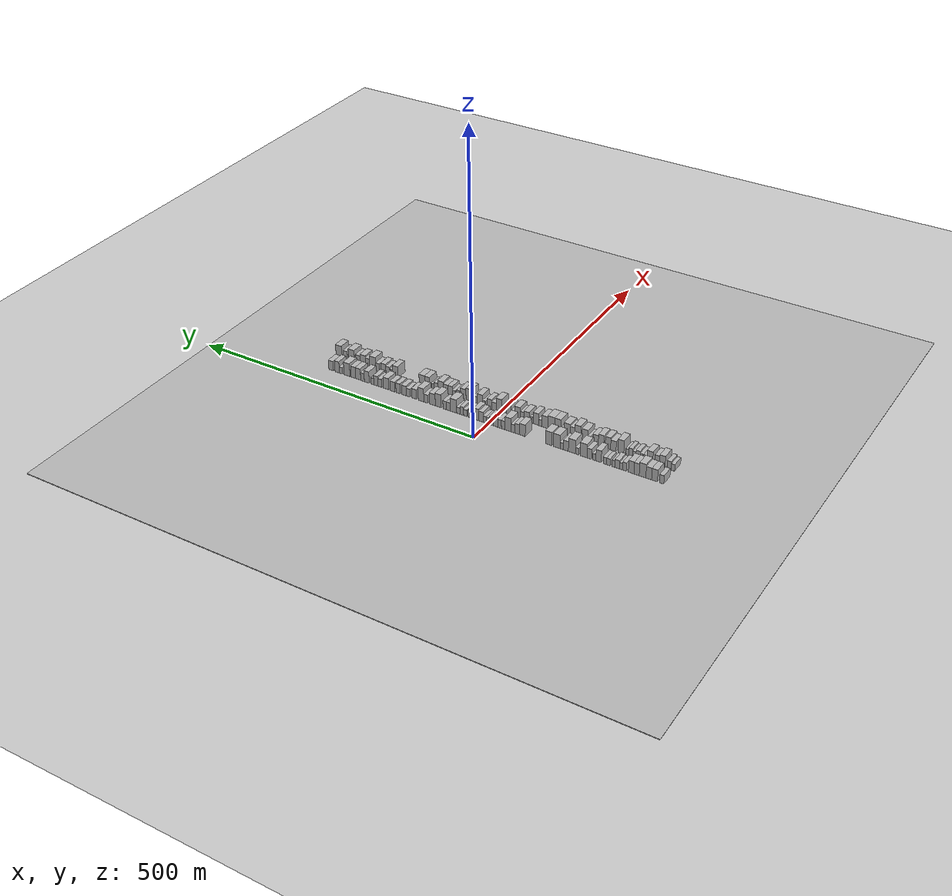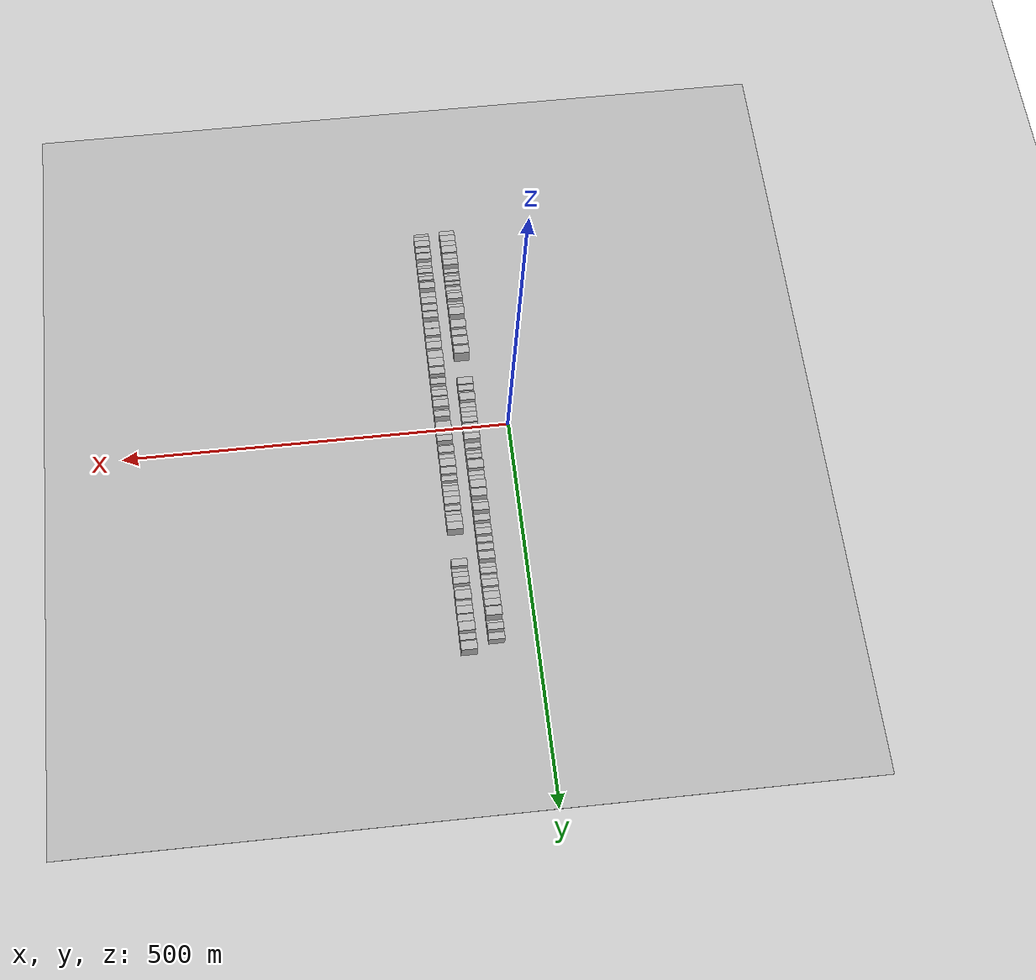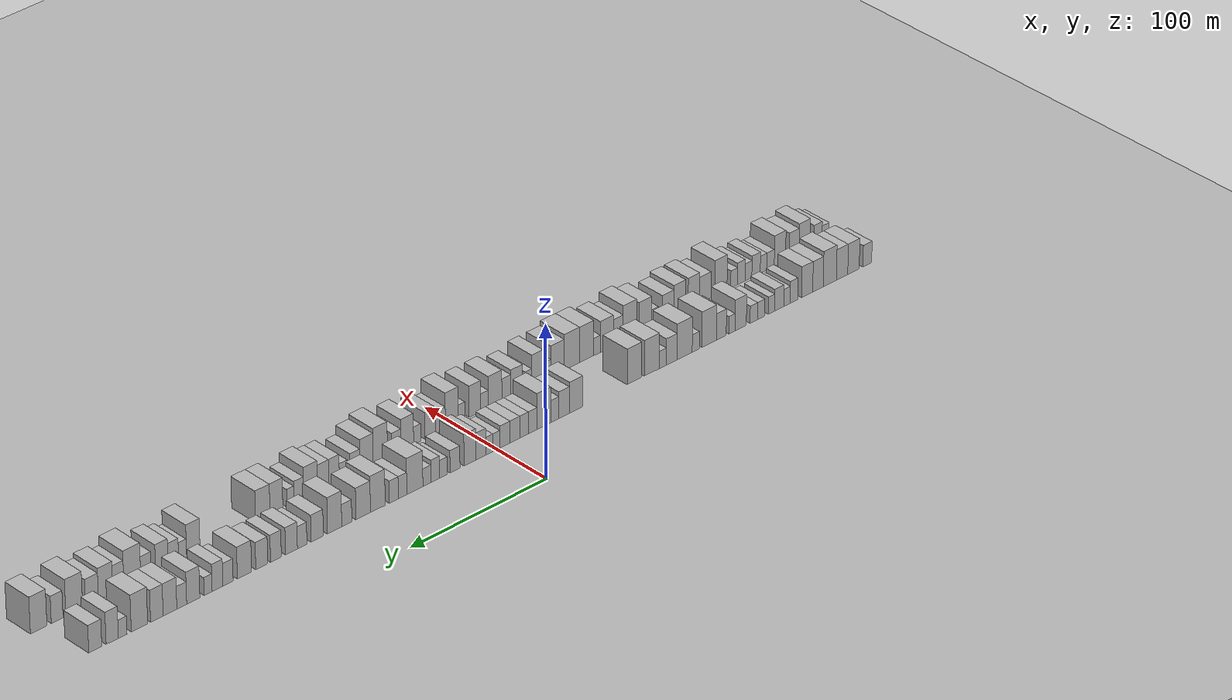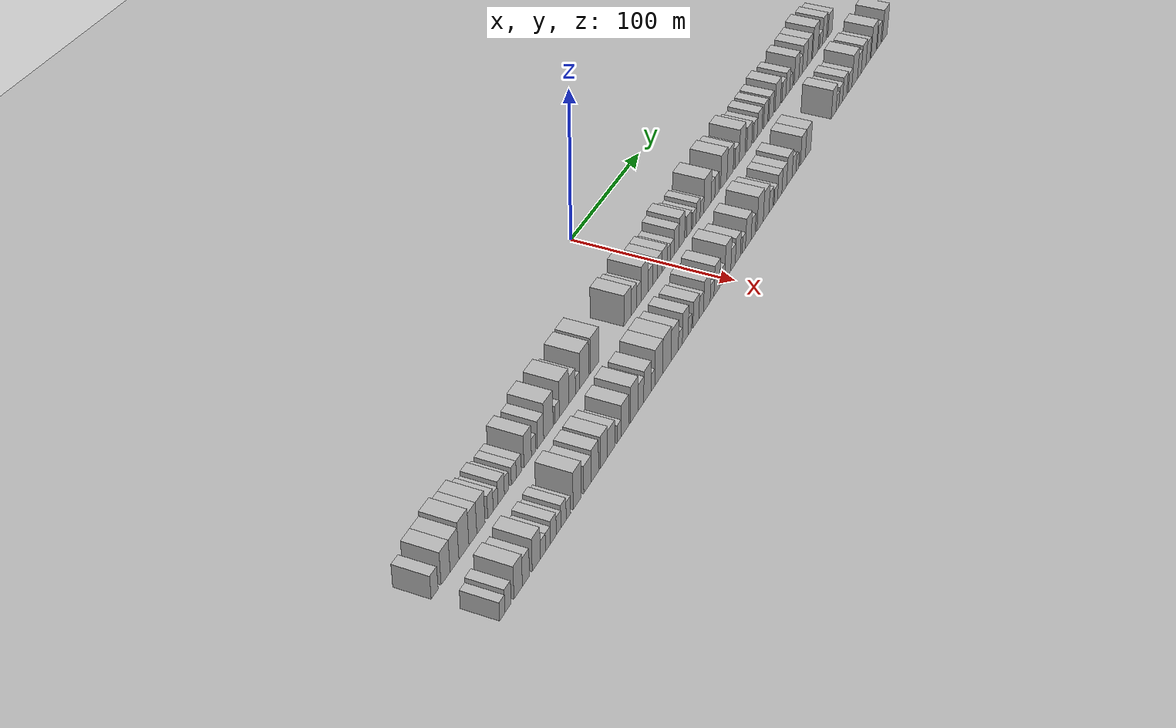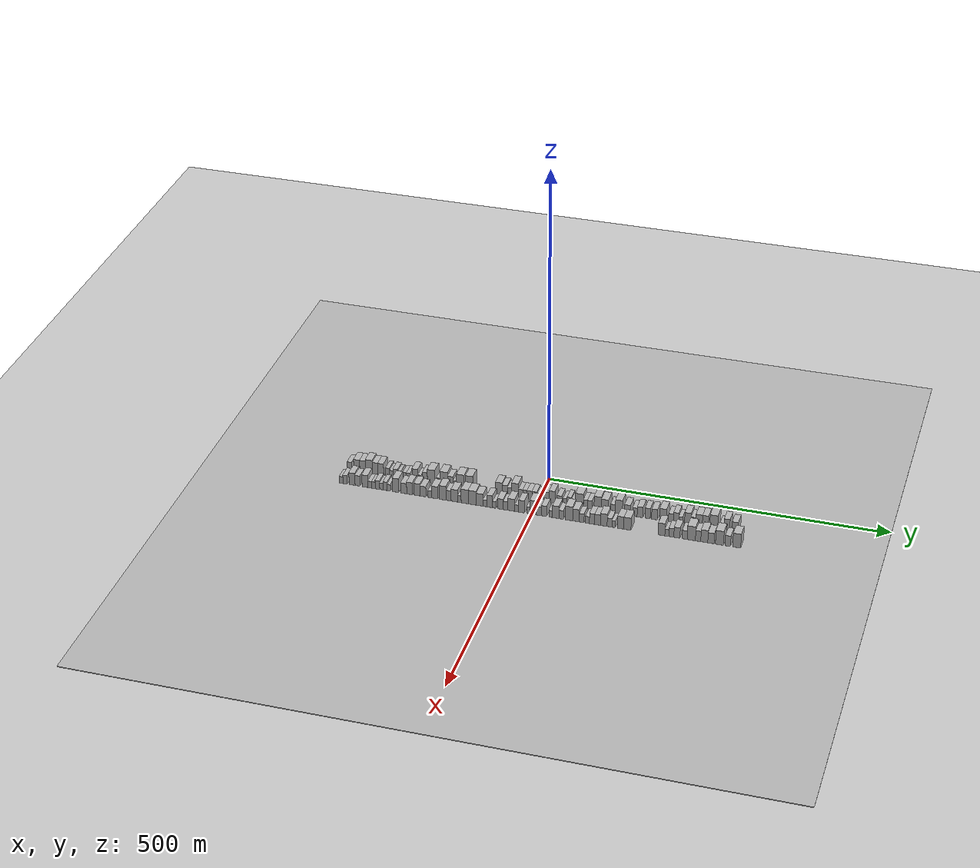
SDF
<?xml version="1.0" encoding="utf-8"?>

<sdf version="1.6">

   <world name="default">

      <gui fullscreen="0">

         <camera name="user_camera">

            <pose>-15 0 4.57585 0 0 0</pose>

            <view_controller>orbit</view_controller>

         </camera>

      </gui>

      <scene>

         <sky>

           <clouds>

             <speed>12</speed>

           </clouds>

         </sky>

         <ambient>0.4 0.4 0.4 1</ambient>

         <background>0.7 0.7 0.7 1</background>

         <shadows>1</shadows>

      </scene>

      <gravity>0 0 -9.8066</gravity>

      <magnetic_field>6e-06 2.3e-05 -4.2e-05</magnetic_field>

      <physics default="0" name="default_physics" type="ode">

         <ode>

            <solver>

               <type>quick</type>

               <iters>10</iters>

               <sor>1.0</sor>

               <use_dynamic_moi_rescaling>0</use_dynamic_moi_rescaling>

            </solver>

            <constraints>

               <cfm>0</cfm>

               <erp>0.2</erp>

               <contact_max_correcting_vel>100</contact_max_correcting_vel>

               <contact_surface_layer>0.001</contact_surface_layer>

            </constraints>

         </ode>

         <max_step_size>0.004</max_step_size>

         <real_time_factor>1</real_time_factor>

         <real_time_update_rate>250</real_time_update_rate>

      </physics>

      <light name="sun" type="directional">

         <cast_shadows>1</cast_shadows>

         <pose>0 0 10 0 0 0</pose>

         <diffuse>0.8 0.8 0.8 1</diffuse>

         <specular>0.2 0.2 0.2 1</specular>

         <attenuation>

            <range>1000</range>

            <constant>0.9</constant>

            <linear>0.01</linear>

            <quadratic>0.001</quadratic>

         </attenuation>

         <direction>-0.5 0.1 -0.9</direction>

      </light>

      <include>

         <name>ground_plane_1</name>

         <uri>model://HANNAS_ground_plane</uri>

         <pose>0 0 0  0 0 0</pose>

      </include>

      <include>

         <name>ground_plane_2</name>

         <uri>model://HANNAS_ground_plane</uri>

         <pose>100 0 0  0 0 0</pose>

      </include>

      <model name="building_1">

         <static>1</static>

         <pose frame="">50.0000 -286.4982 0 0.000000 0.000000 0.000000</pose>

         <link name="link">

            <pose frame="">0 0 7.50 0 0 0</pose>

            <collision name="collision">

               <geometry>

                  <box>

                     <size>20.0000 7.0036 15.0000</size>

                  </box>

               </geometry>

               <max_contacts>10</max_contacts>

               <surface>

                  <contact>

                     <ode/>

                  </contact>

                  <bounce/>

                  <friction>

                     <torsional>

                        <ode/>

                     </torsional>

                     <ode/>

                  </friction>

               </surface>

            </collision>

            <visual name="visual">

               <cast_shadows>0</cast_shadows>

               <geometry>

                  <box>

                     <size>20.0000 7.0036 15.0000</size>

                  </box>

               </geometry>

               <material>

                  <script>

                     <uri>model://HANNAS_wall/materials/scripts</uri>

                     <uri>model://HANNAS_wall/materials/textures</uri>

                     <name>vrc/HANNAS_wall</name>

                  </script>

               </material>

            </visual>

            <self_collide>0</self_collide>

            <enable_wind>0</enable_wind>

            <kinematic>0</kinematic>

         </link>

      </model>

      <model name="building_2">

         <static>1</static>

         <pose frame="">50.0000 -275.3870 0 0.000000 0.000000 0.000000</pose>

         <link name="link">

            <pose frame="">0 0 10.50 0 0 0</pose>

            <collision name="collision">

               <geometry>

                  <box>

                     <size>20.0000 9.2189 21.0000</size>

                  </box>

               </geometry>

               <max_contacts>10</max_contacts>

               <surface>

                  <contact>

                     <ode/>

                  </contact>

                  <bounce/>

                  <friction>

                     <torsional>

                        <ode/>

                     </torsional>

                     <ode/>

                  </friction>

               </surface>

            </collision>

            <visual name="visual">

               <cast_shadows>0</cast_shadows>

               <geometry>

                  <box>

                     <size>20.0000 9.2189 21.0000</size>

                  </box>

               </geometry>

               <material>

                  <script>

                     <uri>model://HANNAS_wall/materials/scripts</uri>

                     <uri>model://HANNAS_wall/materials/textures</uri>

                     <name>vrc/HANNAS_wall</name>

                  </script>

               </material>

            </visual>

            <self_collide>0</self_collide>

            <enable_wind>0</enable_wind>

            <kinematic>0</kinematic>

         </link>

      </model>

      <model name="building_3">

         <static>1</static>

         <pose frame="">50.0000 -266.2587 0 0.000000 0.000000 0.000000</pose>

         <link name="link">

            <pose frame="">0 0 10.50 0 0 0</pose>

            <collision name="collision">

               <geometry>

                  <box>

                     <size>20.0000 9.0376 21.0000</size>

                  </box>

               </geometry>

               <max_contacts>10</max_contacts>

               <surface>

                  <contact>

                     <ode/>

                  </contact>

                  <bounce/>

                  <friction>

                     <torsional>

                        <ode/>

                     </torsional>

                     <ode/>

                  </friction>

               </surface>

            </collision>

            <visual name="visual">

               <cast_shadows>0</cast_shadows>

               <geometry>

                  <box>

                     <size>20.0000 9.0376 21.0000</size>

                  </box>

               </geometry>

               <material>

                  <script>

                     <uri>model://HANNAS_wall/materials/scripts</uri>

                     <uri>model://HANNAS_wall/materials/textures</uri>

                     <name>vrc/HANNAS_wall</name>

                  </script>

               </material>

            </visual>

            <self_collide>0</self_collide>

            <enable_wind>0</enable_wind>

            <kinematic>0</kinematic>

         </link>

      </model>

      <model name="building_4">

         <static>1</static>

         <pose frame="">50.0000 -256.4844 0 0.000000 0.000000 0.000000</pose>

         <link name="link">

            <pose frame="">0 0 12.00 0 0 0</pose>

            <collision name="collision">

               <geometry>

                  <box>

                     <size>20.0000 10.5111 24.0000</size>

                  </box>

               </geometry>

               <max_contacts>10</max_contacts>

               <surface>

                  <contact>

                     <ode/>

                  </contact>

                  <bounce/>

                  <friction>

                     <torsional>

                        <ode/>

                     </torsional>

                     <ode/>

                  </friction>

               </surface>

            </collision>

            <visual name="visual">

               <cast_shadows>0</cast_shadows>

               <geometry>

                  <box>

                     <size>20.0000 10.5111 24.0000</size>

                  </box>

               </geometry>

               <material>

                  <script>

                     <uri>model://HANNAS_wall/materials/scripts</uri>

                     <uri>model://HANNAS_wall/materials/textures</uri>

                     <name>vrc/HANNAS_wall</name>

                  </script>

               </material>

            </visual>

            <self_collide>0</self_collide>

            <enable_wind>0</enable_wind>

            <kinematic>0</kinematic>

         </link>

      </model>

      <model name="building_5">

         <static>1</static>

         <pose frame="">50.0000 -247.0157 0 0.000000 0.000000 0.000000</pose>

         <link name="link">

            <pose frame="">0 0 10.50 0 0 0</pose>

            <collision name="collision">

               <geometry>

                  <box>

                     <size>20.0000 8.4264 21.0000</size>

                  </box>

               </geometry>

               <max_contacts>10</max_contacts>

               <surface>

                  <contact>

                     <ode/>

                  </contact>

                  <bounce/>

                  <friction>

                     <torsional>

                        <ode/>

                     </torsional>

                     <ode/>

                  </friction>

               </surface>

            </collision>

            <visual name="visual">

               <cast_shadows>0</cast_shadows>

               <geometry>

                  <box>

                     <size>20.0000 8.4264 21.0000</size>

                  </box>

               </geometry>

               <material>

                  <script>

                     <uri>model://HANNAS_wall/materials/scripts</uri>

                     <uri>model://HANNAS_wall/materials/textures</uri>

                     <name>vrc/HANNAS_wall</name>

                  </script>

               </material>

            </visual>

            <self_collide>0</self_collide>

            <enable_wind>0</enable_wind>

            <kinematic>0</kinematic>

         </link>

      </model>

      <model name="building_6">

         <static>1</static>

         <pose frame="">50.0000 -238.3939 0 0.000000 0.000000 0.000000</pose>

         <link name="link">

            <pose frame="">0 0 10.50 0 0 0</pose>

            <collision name="collision">

               <geometry>

                  <box>

                     <size>20.0000 8.8172 21.0000</size>

                  </box>

               </geometry>

               <max_contacts>10</max_contacts>

               <surface>

                  <contact>

                     <ode/>

                  </contact>

                  <bounce/>

                  <friction>

                     <torsional>

                        <ode/>

                     </torsional>

                     <ode/>

                  </friction>

               </surface>

            </collision>

            <visual name="visual">

               <cast_shadows>0</cast_shadows>

               <geometry>

                  <box>

                     <size>20.0000 8.8172 21.0000</size>

                  </box>

               </geometry>

               <material>

                  <script>

                     <uri>model://HANNAS_wall/materials/scripts</uri>

                     <uri>model://HANNAS_wall/materials/textures</uri>

                     <name>vrc/HANNAS_wall</name>

                  </script>

               </material>

            </visual>

            <self_collide>0</self_collide>

            <enable_wind>0</enable_wind>

            <kinematic>0</kinematic>

         </link>

      </model>

      <model name="building_7">

         <static>1</static>

         <pose frame="">50.0000 -227.9844 0 0.000000 0.000000 0.000000</pose>

         <link name="link">

            <pose frame="">0 0 7.50 0 0 0</pose>

            <collision name="collision">

               <geometry>

                  <box>

                     <size>20.0000 6.0017 15.0000</size>

                  </box>

               </geometry>

               <max_contacts>10</max_contacts>

               <surface>

                  <contact>

                     <ode/>

                  </contact>

                  <bounce/>

                  <friction>

                     <torsional>

                        <ode/>

                     </torsional>

                     <ode/>

                  </friction>

               </surface>

            </collision>

            <visual name="visual">

               <cast_shadows>0</cast_shadows>

               <geometry>

                  <box>

                     <size>20.0000 6.0017 15.0000</size>

                  </box>

               </geometry>

               <material>

                  <script>

                     <uri>model://HANNAS_wall/materials/scripts</uri>

                     <uri>model://HANNAS_wall/materials/textures</uri>

                     <name>vrc/HANNAS_wall</name>

                  </script>

               </material>

            </visual>

            <self_collide>0</self_collide>

            <enable_wind>0</enable_wind>

            <kinematic>0</kinematic>

         </link>

      </model>

      <model name="building_8">

         <static>1</static>

         <pose frame="">50.0000 -222.3584 0 0.000000 0.000000 0.000000</pose>

         <link name="link">

            <pose frame="">0 0 6.00 0 0 0</pose>

            <collision name="collision">

               <geometry>

                  <box>

                     <size>20.0000 5.2502 12.0000</size>

                  </box>

               </geometry>

               <max_contacts>10</max_contacts>

               <surface>

                  <contact>

                     <ode/>

                  </contact>

                  <bounce/>

                  <friction>

                     <torsional>

                        <ode/>

                     </torsional>

                     <ode/>

                  </friction>

               </surface>

            </collision>

            <visual name="visual">

               <cast_shadows>0</cast_shadows>

               <geometry>

                  <box>

                     <size>20.0000 5.2502 12.0000</size>

                  </box>

               </geometry>

               <material>

                  <script>

                     <uri>model://HANNAS_wall/materials/scripts</uri>

                     <uri>model://HANNAS_wall/materials/textures</uri>

                     <name>vrc/HANNAS_wall</name>

                  </script>

               </material>

            </visual>

            <self_collide>0</self_collide>

            <enable_wind>0</enable_wind>

            <kinematic>0</kinematic>

         </link>

      </model>

      <model name="building_9">

         <static>1</static>

         <pose frame="">50.0000 -216.1610 0 0.000000 0.000000 0.000000</pose>

         <link name="link">

            <pose frame="">0 0 7.50 0 0 0</pose>

            <collision name="collision">

               <geometry>

                  <box>

                     <size>20.0000 7.1447 15.0000</size>

                  </box>

               </geometry>

               <max_contacts>10</max_contacts>

               <surface>

                  <contact>

                     <ode/>

                  </contact>

                  <bounce/>

                  <friction>

                     <torsional>

                        <ode/>

                     </torsional>

                     <ode/>

                  </friction>

               </surface>

            </collision>

            <visual name="visual">

               <cast_shadows>0</cast_shadows>

               <geometry>

                  <box>

                     <size>20.0000 7.1447 15.0000</size>

                  </box>

               </geometry>

               <material>

                  <script>

                     <uri>model://HANNAS_wall/materials/scripts</uri>

                     <uri>model://HANNAS_wall/materials/textures</uri>

                     <name>vrc/HANNAS_wall</name>

                  </script>

               </material>

            </visual>

            <self_collide>0</self_collide>

            <enable_wind>0</enable_wind>

            <kinematic>0</kinematic>

         </link>

      </model>

      <model name="building_10">

         <static>1</static>

         <pose frame="">50.0000 -210.1644 0 0.000000 0.000000 0.000000</pose>

         <link name="link">

            <pose frame="">0 0 6.00 0 0 0</pose>

            <collision name="collision">

               <geometry>

                  <box>

                     <size>20.0000 4.8484 12.0000</size>

                  </box>

               </geometry>

               <max_contacts>10</max_contacts>

               <surface>

                  <contact>

                     <ode/>

                  </contact>

                  <bounce/>

                  <friction>

                     <torsional>

                        <ode/>

                     </torsional>

                     <ode/>

                  </friction>

               </surface>

            </collision>

            <visual name="visual">

               <cast_shadows>0</cast_shadows>

               <geometry>

                  <box>

                     <size>20.0000 4.8484 12.0000</size>

                  </box>

               </geometry>

               <material>

                  <script>

                     <uri>model://HANNAS_wall/materials/scripts</uri>

                     <uri>model://HANNAS_wall/materials/textures</uri>

                     <name>vrc/HANNAS_wall</name>

                  </script>

               </material>

            </visual>

            <self_collide>0</self_collide>

            <enable_wind>0</enable_wind>

            <kinematic>0</kinematic>

         </link>

      </model>

      <model name="building_11">

         <static>1</static>

         <pose frame="">50.0000 -201.9543 0 0.000000 0.000000 0.000000</pose>

         <link name="link">

            <pose frame="">0 0 6.00 0 0 0</pose>

            <collision name="collision">

               <geometry>

                  <box>

                     <size>20.0000 5.5719 12.0000</size>

                  </box>

               </geometry>

               <max_contacts>10</max_contacts>

               <surface>

                  <contact>

                     <ode/>

                  </contact>

                  <bounce/>

                  <friction>

                     <torsional>

                        <ode/>

                     </torsional>

                     <ode/>

                  </friction>

               </surface>

            </collision>

            <visual name="visual">

               <cast_shadows>0</cast_shadows>

               <geometry>

                  <box>

                     <size>20.0000 5.5719 12.0000</size>

                  </box>

               </geometry>

               <material>

                  <script>

                     <uri>model://HANNAS_wall/materials/scripts</uri>

                     <uri>model://HANNAS_wall/materials/textures</uri>

                     <name>vrc/HANNAS_wall</name>

                  </script>

               </material>

            </visual>

            <self_collide>0</self_collide>

            <enable_wind>0</enable_wind>

            <kinematic>0</kinematic>

         </link>

      </model>

      <model name="building_12">

         <static>1</static>

         <pose frame="">50.0000 -196.2528 0 0.000000 0.000000 0.000000</pose>

         <link name="link">

            <pose frame="">0 0 6.00 0 0 0</pose>

            <collision name="collision">

               <geometry>

                  <box>

                     <size>20.0000 5.8311 12.0000</size>

                  </box>

               </geometry>

               <max_contacts>10</max_contacts>

               <surface>

                  <contact>

                     <ode/>

                  </contact>

                  <bounce/>

                  <friction>

                     <torsional>

                        <ode/>

                     </torsional>

                     <ode/>

                  </friction>

               </surface>

            </collision>

            <visual name="visual">

               <cast_shadows>0</cast_shadows>

               <geometry>

                  <box>

                     <size>20.0000 5.8311 12.0000</size>

                  </box>

               </geometry>

               <material>

                  <script>

                     <uri>model://HANNAS_wall/materials/scripts</uri>

                     <uri>model://HANNAS_wall/materials/textures</uri>

                     <name>vrc/HANNAS_wall</name>

                  </script>

               </material>

            </visual>

            <self_collide>0</self_collide>

            <enable_wind>0</enable_wind>

            <kinematic>0</kinematic>

         </link>

      </model>

      <model name="building_13">

         <static>1</static>

         <pose frame="">50.0000 -185.9787 0 0.000000 0.000000 0.000000</pose>

         <link name="link">

            <pose frame="">0 0 10.50 0 0 0</pose>

            <collision name="collision">

               <geometry>

                  <box>

                     <size>20.0000 8.7171 21.0000</size>

                  </box>

               </geometry>

               <max_contacts>10</max_contacts>

               <surface>

                  <contact>

                     <ode/>

                  </contact>

                  <bounce/>

                  <friction>

                     <torsional>

                        <ode/>

                     </torsional>

                     <ode/>

                  </friction>

               </surface>

            </collision>

            <visual name="visual">

               <cast_shadows>0</cast_shadows>

               <geometry>

                  <box>

                     <size>20.0000 8.7171 21.0000</size>

                  </box>

               </geometry>

               <material>

                  <script>

                     <uri>model://HANNAS_wall/materials/scripts</uri>

                     <uri>model://HANNAS_wall/materials/textures</uri>

                     <name>vrc/HANNAS_wall</name>

                  </script>

               </material>

            </visual>

            <self_collide>0</self_collide>

            <enable_wind>0</enable_wind>

            <kinematic>0</kinematic>

         </link>

      </model>

      <model name="building_14">

         <static>1</static>

         <pose frame="">50.0000 -179.1101 0 0.000000 0.000000 0.000000</pose>

         <link name="link">

            <pose frame="">0 0 6.00 0 0 0</pose>

            <collision name="collision">

               <geometry>

                  <box>

                     <size>20.0000 5.0201 12.0000</size>

                  </box>

               </geometry>

               <max_contacts>10</max_contacts>

               <surface>

                  <contact>

                     <ode/>

                  </contact>

                  <bounce/>

                  <friction>

                     <torsional>

                        <ode/>

                     </torsional>

                     <ode/>

                  </friction>

               </surface>

            </collision>

            <visual name="visual">

               <cast_shadows>0</cast_shadows>

               <geometry>

                  <box>

                     <size>20.0000 5.0201 12.0000</size>

                  </box>

               </geometry>

               <material>

                  <script>

                     <uri>model://HANNAS_wall/materials/scripts</uri>

                     <uri>model://HANNAS_wall/materials/textures</uri>

                     <name>vrc/HANNAS_wall</name>

                  </script>

               </material>

            </visual>

            <self_collide>0</self_collide>

            <enable_wind>0</enable_wind>

            <kinematic>0</kinematic>

         </link>

      </model>

      <model name="building_15">

         <static>1</static>

         <pose frame="">50.0000 -170.8484 0 0.000000 0.000000 0.000000</pose>

         <link name="link">

            <pose frame="">0 0 9.00 0 0 0</pose>

            <collision name="collision">

               <geometry>

                  <box>

                     <size>20.0000 7.5033 18.0000</size>

                  </box>

               </geometry>

               <max_contacts>10</max_contacts>

               <surface>

                  <contact>

                     <ode/>

                  </contact>

                  <bounce/>

                  <friction>

                     <torsional>

                        <ode/>

                     </torsional>

                     <ode/>

                  </friction>

               </surface>

            </collision>

            <visual name="visual">

               <cast_shadows>0</cast_shadows>

               <geometry>

                  <box>

                     <size>20.0000 7.5033 18.0000</size>

                  </box>

               </geometry>

               <material>

                  <script>

                     <uri>model://HANNAS_wall/materials/scripts</uri>

                     <uri>model://HANNAS_wall/materials/textures</uri>

                     <name>vrc/HANNAS_wall</name>

                  </script>

               </material>

            </visual>

            <self_collide>0</self_collide>

            <enable_wind>0</enable_wind>

            <kinematic>0</kinematic>

         </link>

      </model>

      <model name="building_16">

         <static>1</static>

         <pose frame="">50.0000 -161.3963 0 0.000000 0.000000 0.000000</pose>

         <link name="link">

            <pose frame="">0 0 12.00 0 0 0</pose>

            <collision name="collision">

               <geometry>

                  <box>

                     <size>20.0000 11.4009 24.0000</size>

                  </box>

               </geometry>

               <max_contacts>10</max_contacts>

               <surface>

                  <contact>

                     <ode/>

                  </contact>

                  <bounce/>

                  <friction>

                     <torsional>

                        <ode/>

                     </torsional>

                     <ode/>

                  </friction>

               </surface>

            </collision>

            <visual name="visual">

               <cast_shadows>0</cast_shadows>

               <geometry>

                  <box>

                     <size>20.0000 11.4009 24.0000</size>

                  </box>

               </geometry>

               <material>

                  <script>

                     <uri>model://HANNAS_wall/materials/scripts</uri>

                     <uri>model://HANNAS_wall/materials/textures</uri>

                     <name>vrc/HANNAS_wall</name>

                  </script>

               </material>

            </visual>

            <self_collide>0</self_collide>

            <enable_wind>0</enable_wind>

            <kinematic>0</kinematic>

         </link>

      </model>

      <model name="building_17">

         <static>1</static>

         <pose frame="">50.0000 -150.9021 0 0.000000 0.000000 0.000000</pose>

         <link name="link">

            <pose frame="">0 0 6.00 0 0 0</pose>

            <collision name="collision">

               <geometry>

                  <box>

                     <size>20.0000 5.5875 12.0000</size>

                  </box>

               </geometry>

               <max_contacts>10</max_contacts>

               <surface>

                  <contact>

                     <ode/>

                  </contact>

                  <bounce/>

                  <friction>

                     <torsional>

                        <ode/>

                     </torsional>

                     <ode/>

                  </friction>

               </surface>

            </collision>

            <visual name="visual">

               <cast_shadows>0</cast_shadows>

               <geometry>

                  <box>

                     <size>20.0000 5.5875 12.0000</size>

                  </box>

               </geometry>

               <material>

                  <script>

                     <uri>model://HANNAS_wall/materials/scripts</uri>

                     <uri>model://HANNAS_wall/materials/textures</uri>

                     <name>vrc/HANNAS_wall</name>

                  </script>

               </material>

            </visual>

            <self_collide>0</self_collide>

            <enable_wind>0</enable_wind>

            <kinematic>0</kinematic>

         </link>

      </model>

      <model name="building_18">

         <static>1</static>

         <pose frame="">50.0000 -142.2736 0 0.000000 0.000000 0.000000</pose>

         <link name="link">

            <pose frame="">0 0 12.00 0 0 0</pose>

            <collision name="collision">

               <geometry>

                  <box>

                     <size>20.0000 11.6695 24.0000</size>

                  </box>

               </geometry>

               <max_contacts>10</max_contacts>

               <surface>

                  <contact>

                     <ode/>

                  </contact>

                  <bounce/>

                  <friction>

                     <torsional>

                        <ode/>

                     </torsional>

                     <ode/>

                  </friction>

               </surface>

            </collision>

            <visual name="visual">

               <cast_shadows>0</cast_shadows>

               <geometry>

                  <box>

                     <size>20.0000 11.6695 24.0000</size>

                  </box>

               </geometry>

               <material>

                  <script>

                     <uri>model://HANNAS_wall/materials/scripts</uri>

                     <uri>model://HANNAS_wall/materials/textures</uri>

                     <name>vrc/HANNAS_wall</name>

                  </script>

               </material>

            </visual>

            <self_collide>0</self_collide>

            <enable_wind>0</enable_wind>

            <kinematic>0</kinematic>

         </link>

      </model>

      <model name="building_19">

         <static>1</static>

         <pose frame="">50.0000 -132.2392 0 0.000000 0.000000 0.000000</pose>

         <link name="link">

            <pose frame="">0 0 9.00 0 0 0</pose>

            <collision name="collision">

               <geometry>

                  <box>

                     <size>20.0000 8.3993 18.0000</size>

                  </box>

               </geometry>

               <max_contacts>10</max_contacts>

               <surface>

                  <contact>

                     <ode/>

                  </contact>

                  <bounce/>

                  <friction>

                     <torsional>

                        <ode/>

                     </torsional>

                     <ode/>

                  </friction>

               </surface>

            </collision>

            <visual name="visual">

               <cast_shadows>0</cast_shadows>

               <geometry>

                  <box>

                     <size>20.0000 8.3993 18.0000</size>

                  </box>

               </geometry>

               <material>

                  <script>

                     <uri>model://HANNAS_wall/materials/scripts</uri>

                     <uri>model://HANNAS_wall/materials/textures</uri>

                     <name>vrc/HANNAS_wall</name>

                  </script>

               </material>

            </visual>

            <self_collide>0</self_collide>

            <enable_wind>0</enable_wind>

            <kinematic>0</kinematic>

         </link>

      </model>

      <model name="building_20">

         <static>1</static>

         <pose frame="">50.0000 -125.4247 0 0.000000 0.000000 0.000000</pose>

         <link name="link">

            <pose frame="">0 0 6.00 0 0 0</pose>

            <collision name="collision">

               <geometry>

                  <box>

                     <size>20.0000 5.2296 12.0000</size>

                  </box>

               </geometry>

               <max_contacts>10</max_contacts>

               <surface>

                  <contact>

                     <ode/>

                  </contact>

                  <bounce/>

                  <friction>

                     <torsional>

                        <ode/>

                     </torsional>

                     <ode/>

                  </friction>

               </surface>

            </collision>

            <visual name="visual">

               <cast_shadows>0</cast_shadows>

               <geometry>

                  <box>

                     <size>20.0000 5.2296 12.0000</size>

                  </box>

               </geometry>

               <material>

                  <script>

                     <uri>model://HANNAS_wall/materials/scripts</uri>

                     <uri>model://HANNAS_wall/materials/textures</uri>

                     <name>vrc/HANNAS_wall</name>

                  </script>

               </material>

            </visual>

            <self_collide>0</self_collide>

            <enable_wind>0</enable_wind>

            <kinematic>0</kinematic>

         </link>

      </model>

      <model name="building_21">

         <static>1</static>

         <pose frame="">50.0000 -117.0029 0 0.000000 0.000000 0.000000</pose>

         <link name="link">

            <pose frame="">0 0 12.00 0 0 0</pose>

            <collision name="collision">

               <geometry>

                  <box>

                     <size>20.0000 11.6140 24.0000</size>

                  </box>

               </geometry>

               <max_contacts>10</max_contacts>

               <surface>

                  <contact>

                     <ode/>

                  </contact>

                  <bounce/>

                  <friction>

                     <torsional>

                        <ode/>

                     </torsional>

                     <ode/>

                  </friction>

               </surface>

            </collision>

            <visual name="visual">

               <cast_shadows>0</cast_shadows>

               <geometry>

                  <box>

                     <size>20.0000 11.6140 24.0000</size>

                  </box>

               </geometry>

               <material>

                  <script>

                     <uri>model://HANNAS_wall/materials/scripts</uri>

                     <uri>model://HANNAS_wall/materials/textures</uri>

                     <name>vrc/HANNAS_wall</name>

                  </script>

               </material>

            </visual>

            <self_collide>0</self_collide>

            <enable_wind>0</enable_wind>

            <kinematic>0</kinematic>

         </link>

      </model>

      <model name="building_22">

         <static>1</static>

         <pose frame="">50.0000 -103.6227 0 0.000000 0.000000 0.000000</pose>

         <link name="link">

            <pose frame="">0 0 12.00 0 0 0</pose>

            <collision name="collision">

               <geometry>

                  <box>

                     <size>20.0000 11.1463 24.0000</size>

                  </box>

               </geometry>

               <max_contacts>10</max_contacts>

               <surface>

                  <contact>

                     <ode/>

                  </contact>

                  <bounce/>

                  <friction>

                     <torsional>

                        <ode/>

                     </torsional>

                     <ode/>

                  </friction>

               </surface>

            </collision>

            <visual name="visual">

               <cast_shadows>0</cast_shadows>

               <geometry>

                  <box>

                     <size>20.0000 11.1463 24.0000</size>

                  </box>

               </geometry>

               <material>

                  <script>

                     <uri>model://HANNAS_wall/materials/scripts</uri>

                     <uri>model://HANNAS_wall/materials/textures</uri>

                     <name>vrc/HANNAS_wall</name>

                  </script>

               </material>

            </visual>

            <self_collide>0</self_collide>

            <enable_wind>0</enable_wind>

            <kinematic>0</kinematic>

         </link>

      </model>

      <model name="building_23">

         <static>1</static>

         <pose frame="">50.0000 -59.1376 0 0.000000 0.000000 0.000000</pose>

         <link name="link">

            <pose frame="">0 0 10.50 0 0 0</pose>

            <collision name="collision">

               <geometry>

                  <box>

                     <size>20.0000 9.9413 21.0000</size>

                  </box>

               </geometry>

               <max_contacts>10</max_contacts>

               <surface>

                  <contact>

                     <ode/>

                  </contact>

                  <bounce/>

                  <friction>

                     <torsional>

                        <ode/>

                     </torsional>

                     <ode/>

                  </friction>

               </surface>

            </collision>

            <visual name="visual">

               <cast_shadows>0</cast_shadows>

               <geometry>

                  <box>

                     <size>20.0000 9.9413 21.0000</size>

                  </box>

               </geometry>

               <material>

                  <script>

                     <uri>model://HANNAS_wall/materials/scripts</uri>

                     <uri>model://HANNAS_wall/materials/textures</uri>

                     <name>vrc/HANNAS_wall</name>

                  </script>

               </material>

            </visual>

            <self_collide>0</self_collide>

            <enable_wind>0</enable_wind>

            <kinematic>0</kinematic>

         </link>

      </model>

      <model name="building_24">

         <static>1</static>

         <pose frame="">50.0000 -50.2014 0 0.000000 0.000000 0.000000</pose>

         <link name="link">

            <pose frame="">0 0 9.00 0 0 0</pose>

            <collision name="collision">

               <geometry>

                  <box>

                     <size>20.0000 7.9310 18.0000</size>

                  </box>

               </geometry>

               <max_contacts>10</max_contacts>

               <surface>

                  <contact>

                     <ode/>

                  </contact>

                  <bounce/>

                  <friction>

                     <torsional>

                        <ode/>

                     </torsional>

                     <ode/>

                  </friction>

               </surface>

            </collision>

            <visual name="visual">

               <cast_shadows>0</cast_shadows>

               <geometry>

                  <box>

                     <size>20.0000 7.9310 18.0000</size>

                  </box>

               </geometry>

               <material>

                  <script>

                     <uri>model://HANNAS_wall/materials/scripts</uri>

                     <uri>model://HANNAS_wall/materials/textures</uri>

                     <name>vrc/HANNAS_wall</name>

                  </script>

               </material>

            </visual>

            <self_collide>0</self_collide>

            <enable_wind>0</enable_wind>

            <kinematic>0</kinematic>

         </link>

      </model>

      <model name="building_25">

         <static>1</static>

         <pose frame="">50.0000 -43.1942 0 0.000000 0.000000 0.000000</pose>

         <link name="link">

            <pose frame="">0 0 7.50 0 0 0</pose>

            <collision name="collision">

               <geometry>

                  <box>

                     <size>20.0000 6.0834 15.0000</size>

                  </box>

               </geometry>

               <max_contacts>10</max_contacts>

               <surface>

                  <contact>

                     <ode/>

                  </contact>

                  <bounce/>

                  <friction>

                     <torsional>

                        <ode/>

                     </torsional>

                     <ode/>

                  </friction>

               </surface>

            </collision>

            <visual name="visual">

               <cast_shadows>0</cast_shadows>

               <geometry>

                  <box>

                     <size>20.0000 6.0834 15.0000</size>

                  </box>

               </geometry>

               <material>

                  <script>

                     <uri>model://HANNAS_wall/materials/scripts</uri>

                     <uri>model://HANNAS_wall/materials/textures</uri>

                     <name>vrc/HANNAS_wall</name>

                  </script>

               </material>

            </visual>

            <self_collide>0</self_collide>

            <enable_wind>0</enable_wind>

            <kinematic>0</kinematic>

         </link>

      </model>

      <model name="building_26">

         <static>1</static>

         <pose frame="">50.0000 -34.9737 0 0.000000 0.000000 0.000000</pose>

         <link name="link">

            <pose frame="">0 0 12.00 0 0 0</pose>

            <collision name="collision">

               <geometry>

                  <box>

                     <size>20.0000 10.3576 24.0000</size>

                  </box>

               </geometry>

               <max_contacts>10</max_contacts>

               <surface>

                  <contact>

                     <ode/>

                  </contact>

                  <bounce/>

                  <friction>

                     <torsional>

                        <ode/>

                     </torsional>

                     <ode/>

                  </friction>

               </surface>

            </collision>

            <visual name="visual">

               <cast_shadows>0</cast_shadows>

               <geometry>

                  <box>

                     <size>20.0000 10.3576 24.0000</size>

                  </box>

               </geometry>

               <material>

                  <script>

                     <uri>model://HANNAS_wall/materials/scripts</uri>

                     <uri>model://HANNAS_wall/materials/textures</uri>

                     <name>vrc/HANNAS_wall</name>

                  </script>

               </material>

            </visual>

            <self_collide>0</self_collide>

            <enable_wind>0</enable_wind>

            <kinematic>0</kinematic>

         </link>

      </model>

      <model name="building_27">

         <static>1</static>

         <pose frame="">50.0000 -26.5059 0 0.000000 0.000000 0.000000</pose>

         <link name="link">

            <pose frame="">0 0 7.50 0 0 0</pose>

            <collision name="collision">

               <geometry>

                  <box>

                     <size>20.0000 6.5779 15.0000</size>

                  </box>

               </geometry>

               <max_contacts>10</max_contacts>

               <surface>

                  <contact>

                     <ode/>

                  </contact>

                  <bounce/>

                  <friction>

                     <torsional>

                        <ode/>

                     </torsional>

                     <ode/>

                  </friction>

               </surface>

            </collision>

            <visual name="visual">

               <cast_shadows>0</cast_shadows>

               <geometry>

                  <box>

                     <size>20.0000 6.5779 15.0000</size>

                  </box>

               </geometry>

               <material>

                  <script>

                     <uri>model://HANNAS_wall/materials/scripts</uri>

                     <uri>model://HANNAS_wall/materials/textures</uri>

                     <name>vrc/HANNAS_wall</name>

                  </script>

               </material>

            </visual>

            <self_collide>0</self_collide>

            <enable_wind>0</enable_wind>

            <kinematic>0</kinematic>

         </link>

      </model>

      <model name="building_28">

         <static>1</static>

         <pose frame="">50.0000 -19.9818 0 0.000000 0.000000 0.000000</pose>

         <link name="link">

            <pose frame="">0 0 7.50 0 0 0</pose>

            <collision name="collision">

               <geometry>

                  <box>

                     <size>20.0000 6.4703 15.0000</size>

                  </box>

               </geometry>

               <max_contacts>10</max_contacts>

               <surface>

                  <contact>

                     <ode/>

                  </contact>

                  <bounce/>

                  <friction>

                     <torsional>

                        <ode/>

                     </torsional>

                     <ode/>

                  </friction>

               </surface>

            </collision>

            <visual name="visual">

               <cast_shadows>0</cast_shadows>

               <geometry>

                  <box>

                     <size>20.0000 6.4703 15.0000</size>

                  </box>

               </geometry>

               <material>

                  <script>

                     <uri>model://HANNAS_wall/materials/scripts</uri>

                     <uri>model://HANNAS_wall/materials/textures</uri>

                     <name>vrc/HANNAS_wall</name>

                  </script>

               </material>

            </visual>

            <self_collide>0</self_collide>

            <enable_wind>0</enable_wind>

            <kinematic>0</kinematic>

         </link>

      </model>

      <model name="building_29">

         <static>1</static>

         <pose frame="">50.0000 -13.1419 0 0.000000 0.000000 0.000000</pose>

         <link name="link">

            <pose frame="">0 0 7.50 0 0 0</pose>

            <collision name="collision">

               <geometry>

                  <box>

                     <size>20.0000 7.2096 15.0000</size>

                  </box>

               </geometry>

               <max_contacts>10</max_contacts>

               <surface>

                  <contact>

                     <ode/>

                  </contact>

                  <bounce/>

                  <friction>

                     <torsional>

                        <ode/>

                     </torsional>

                     <ode/>

                  </friction>

               </surface>

            </collision>

            <visual name="visual">

               <cast_shadows>0</cast_shadows>

               <geometry>

                  <box>

                     <size>20.0000 7.2096 15.0000</size>

                  </box>

               </geometry>

               <material>

                  <script>

                     <uri>model://HANNAS_wall/materials/scripts</uri>

                     <uri>model://HANNAS_wall/materials/textures</uri>

                     <name>vrc/HANNAS_wall</name>

                  </script>

               </material>

            </visual>

            <self_collide>0</self_collide>

            <enable_wind>0</enable_wind>

            <kinematic>0</kinematic>

         </link>

      </model>

      <model name="building_30">

         <static>1</static>

         <pose frame="">50.0000 -5.8163 0 0.000000 0.000000 0.000000</pose>

         <link name="link">

            <pose frame="">0 0 7.50 0 0 0</pose>

            <collision name="collision">

               <geometry>

                  <box>

                     <size>20.0000 7.4415 15.0000</size>

                  </box>

               </geometry>

               <max_contacts>10</max_contacts>

               <surface>

                  <contact>

                     <ode/>

                  </contact>

                  <bounce/>

                  <friction>

                     <torsional>

                        <ode/>

                     </torsional>

                     <ode/>

                  </friction>

               </surface>

            </collision>

            <visual name="visual">

               <cast_shadows>0</cast_shadows>

               <geometry>

                  <box>

                     <size>20.0000 7.4415 15.0000</size>

                  </box>

               </geometry>

               <material>

                  <script>

                     <uri>model://HANNAS_wall/materials/scripts</uri>

                     <uri>model://HANNAS_wall/materials/textures</uri>

                     <name>vrc/HANNAS_wall</name>

                  </script>

               </material>

            </visual>

            <self_collide>0</self_collide>

            <enable_wind>0</enable_wind>

            <kinematic>0</kinematic>

         </link>

      </model>

      <model name="building_31">

         <static>1</static>

         <pose frame="">50.0000 0.5402 0 0.000000 0.000000 0.000000</pose>

         <link name="link">

            <pose frame="">0 0 6.00 0 0 0</pose>

            <collision name="collision">

               <geometry>

                  <box>

                     <size>20.0000 5.2715 12.0000</size>

                  </box>

               </geometry>

               <max_contacts>10</max_contacts>

               <surface>

                  <contact>

                     <ode/>

                  </contact>

                  <bounce/>

                  <friction>

                     <torsional>

                        <ode/>

                     </torsional>

                     <ode/>

                  </friction>

               </surface>

            </collision>

            <visual name="visual">

               <cast_shadows>0</cast_shadows>

               <geometry>

                  <box>

                     <size>20.0000 5.2715 12.0000</size>

                  </box>

               </geometry>

               <material>

                  <script>

                     <uri>model://HANNAS_wall/materials/scripts</uri>

                     <uri>model://HANNAS_wall/materials/textures</uri>

                     <name>vrc/HANNAS_wall</name>

                  </script>

               </material>

            </visual>

            <self_collide>0</self_collide>

            <enable_wind>0</enable_wind>

            <kinematic>0</kinematic>

         </link>

      </model>

      <model name="building_32">

         <static>1</static>

         <pose frame="">50.0000 5.8789 0 0.000000 0.000000 0.000000</pose>

         <link name="link">

            <pose frame="">0 0 6.00 0 0 0</pose>

            <collision name="collision">

               <geometry>

                  <box>

                     <size>20.0000 5.4058 12.0000</size>

                  </box>

               </geometry>

               <max_contacts>10</max_contacts>

               <surface>

                  <contact>

                     <ode/>

                  </contact>

                  <bounce/>

                  <friction>

                     <torsional>

                        <ode/>

                     </torsional>

                     <ode/>

                  </friction>

               </surface>

            </collision>

            <visual name="visual">

               <cast_shadows>0</cast_shadows>

               <geometry>

                  <box>

                     <size>20.0000 5.4058 12.0000</size>

                  </box>

               </geometry>

               <material>

                  <script>

                     <uri>model://HANNAS_wall/materials/scripts</uri>

                     <uri>model://HANNAS_wall/materials/textures</uri>

                     <name>vrc/HANNAS_wall</name>

                  </script>

               </material>

            </visual>

            <self_collide>0</self_collide>

            <enable_wind>0</enable_wind>

            <kinematic>0</kinematic>

         </link>

      </model>

      <model name="building_33">

         <static>1</static>

         <pose frame="">50.0000 12.2712 0 0.000000 0.000000 0.000000</pose>

         <link name="link">

            <pose frame="">0 0 9.00 0 0 0</pose>

            <collision name="collision">

               <geometry>

                  <box>

                     <size>20.0000 7.3789 18.0000</size>

                  </box>

               </geometry>

               <max_contacts>10</max_contacts>

               <surface>

                  <contact>

                     <ode/>

                  </contact>

                  <bounce/>

                  <friction>

                     <torsional>

                        <ode/>

                     </torsional>

                     <ode/>

                  </friction>

               </surface>

            </collision>

            <visual name="visual">

               <cast_shadows>0</cast_shadows>

               <geometry>

                  <box>

                     <size>20.0000 7.3789 18.0000</size>

                  </box>

               </geometry>

               <material>

                  <script>

                     <uri>model://HANNAS_wall/materials/scripts</uri>

                     <uri>model://HANNAS_wall/materials/textures</uri>

                     <name>vrc/HANNAS_wall</name>

                  </script>

               </material>

            </visual>

            <self_collide>0</self_collide>

            <enable_wind>0</enable_wind>

            <kinematic>0</kinematic>

         </link>

      </model>

      <model name="building_34">

         <static>1</static>

         <pose frame="">50.0000 20.3390 0 0.000000 0.000000 0.000000</pose>

         <link name="link">

            <pose frame="">0 0 10.50 0 0 0</pose>

            <collision name="collision">

               <geometry>

                  <box>

                     <size>20.0000 8.7569 21.0000</size>

                  </box>

               </geometry>

               <max_contacts>10</max_contacts>

               <surface>

                  <contact>

                     <ode/>

                  </contact>

                  <bounce/>

                  <friction>

                     <torsional>

                        <ode/>

                     </torsional>

                     <ode/>

                  </friction>

               </surface>

            </collision>

            <visual name="visual">

               <cast_shadows>0</cast_shadows>

               <geometry>

                  <box>

                     <size>20.0000 8.7569 21.0000</size>

                  </box>

               </geometry>

               <material>

                  <script>

                     <uri>model://HANNAS_wall/materials/scripts</uri>

                     <uri>model://HANNAS_wall/materials/textures</uri>

                     <name>vrc/HANNAS_wall</name>

                  </script>

               </material>

            </visual>

            <self_collide>0</self_collide>

            <enable_wind>0</enable_wind>

            <kinematic>0</kinematic>

         </link>

      </model>

      <model name="building_35">

         <static>1</static>

         <pose frame="">50.0000 31.3894 0 0.000000 0.000000 0.000000</pose>

         <link name="link">

            <pose frame="">0 0 7.50 0 0 0</pose>

            <collision name="collision">

               <geometry>

                  <box>

                     <size>20.0000 7.3439 15.0000</size>

                  </box>

               </geometry>

               <max_contacts>10</max_contacts>

               <surface>

                  <contact>

                     <ode/>

                  </contact>

                  <bounce/>

                  <friction>

                     <torsional>

                        <ode/>

                     </torsional>

                     <ode/>

                  </friction>

               </surface>

            </collision>

            <visual name="visual">

               <cast_shadows>0</cast_shadows>

               <geometry>

                  <box>

                     <size>20.0000 7.3439 15.0000</size>

                  </box>

               </geometry>

               <material>

                  <script>

                     <uri>model://HANNAS_wall/materials/scripts</uri>

                     <uri>model://HANNAS_wall/materials/textures</uri>

                     <name>vrc/HANNAS_wall</name>

                  </script>

               </material>

            </visual>

            <self_collide>0</self_collide>

            <enable_wind>0</enable_wind>

            <kinematic>0</kinematic>

         </link>

      </model>

      <model name="building_36">

         <static>1</static>

         <pose frame="">50.0000 39.9124 0 0.000000 0.000000 0.000000</pose>

         <link name="link">

            <pose frame="">0 0 6.00 0 0 0</pose>

            <collision name="collision">

               <geometry>

                  <box>

                     <size>20.0000 5.7020 12.0000</size>

                  </box>

               </geometry>

               <max_contacts>10</max_contacts>

               <surface>

                  <contact>

                     <ode/>

                  </contact>

                  <bounce/>

                  <friction>

                     <torsional>

                        <ode/>

                     </torsional>

                     <ode/>

                  </friction>

               </surface>

            </collision>

            <visual name="visual">

               <cast_shadows>0</cast_shadows>

               <geometry>

                  <box>

                     <size>20.0000 5.7020 12.0000</size>

                  </box>

               </geometry>

               <material>

                  <script>

                     <uri>model://HANNAS_wall/materials/scripts</uri>

                     <uri>model://HANNAS_wall/materials/textures</uri>

                     <name>vrc/HANNAS_wall</name>

                  </script>

               </material>

            </visual>

            <self_collide>0</self_collide>

            <enable_wind>0</enable_wind>

            <kinematic>0</kinematic>

         </link>

      </model>

      <model name="building_37">

         <static>1</static>

         <pose frame="">50.0000 45.9449 0 0.000000 0.000000 0.000000</pose>

         <link name="link">

            <pose frame="">0 0 7.50 0 0 0</pose>

            <collision name="collision">

               <geometry>

                  <box>

                     <size>20.0000 6.3630 15.0000</size>

                  </box>

               </geometry>

               <max_contacts>10</max_contacts>

               <surface>

                  <contact>

                     <ode/>

                  </contact>

                  <bounce/>

                  <friction>

                     <torsional>

                        <ode/>

                     </torsional>

                     <ode/>

                  </friction>

               </surface>

            </collision>

            <visual name="visual">

               <cast_shadows>0</cast_shadows>

               <geometry>

                  <box>

                     <size>20.0000 6.3630 15.0000</size>

                  </box>

               </geometry>

               <material>

                  <script>

                     <uri>model://HANNAS_wall/materials/scripts</uri>

                     <uri>model://HANNAS_wall/materials/textures</uri>

                     <name>vrc/HANNAS_wall</name>

                  </script>

               </material>

            </visual>

            <self_collide>0</self_collide>

            <enable_wind>0</enable_wind>

            <kinematic>0</kinematic>

         </link>

      </model>

      <model name="building_38">

         <static>1</static>

         <pose frame="">50.0000 52.0841 0 0.000000 0.000000 0.000000</pose>

         <link name="link">

            <pose frame="">0 0 6.00 0 0 0</pose>

            <collision name="collision">

               <geometry>

                  <box>

                     <size>20.0000 5.9154 12.0000</size>

                  </box>

               </geometry>

               <max_contacts>10</max_contacts>

               <surface>

                  <contact>

                     <ode/>

                  </contact>

                  <bounce/>

                  <friction>

                     <torsional>

                        <ode/>

                     </torsional>

                     <ode/>

                  </friction>

               </surface>

            </collision>

            <visual name="visual">

               <cast_shadows>0</cast_shadows>

               <geometry>

                  <box>

                     <size>20.0000 5.9154 12.0000</size>

                  </box>

               </geometry>

               <material>

                  <script>

                     <uri>model://HANNAS_wall/materials/scripts</uri>

                     <uri>model://HANNAS_wall/materials/textures</uri>

                     <name>vrc/HANNAS_wall</name>

                  </script>

               </material>

            </visual>

            <self_collide>0</self_collide>

            <enable_wind>0</enable_wind>

            <kinematic>0</kinematic>

         </link>

      </model>

      <model name="building_39">

         <static>1</static>

         <pose frame="">50.0000 60.9253 0 0.000000 0.000000 0.000000</pose>

         <link name="link">

            <pose frame="">0 0 12.00 0 0 0</pose>

            <collision name="collision">

               <geometry>

                  <box>

                     <size>20.0000 11.7671 24.0000</size>

                  </box>

               </geometry>

               <max_contacts>10</max_contacts>

               <surface>

                  <contact>

                     <ode/>

                  </contact>

                  <bounce/>

                  <friction>

                     <torsional>

                        <ode/>

                     </torsional>

                     <ode/>

                  </friction>

               </surface>

            </collision>

            <visual name="visual">

               <cast_shadows>0</cast_shadows>

               <geometry>

                  <box>

                     <size>20.0000 11.7671 24.0000</size>

                  </box>

               </geometry>

               <material>

                  <script>

                     <uri>model://HANNAS_wall/materials/scripts</uri>

                     <uri>model://HANNAS_wall/materials/textures</uri>

                     <name>vrc/HANNAS_wall</name>

                  </script>

               </material>

            </visual>

            <self_collide>0</self_collide>

            <enable_wind>0</enable_wind>

            <kinematic>0</kinematic>

         </link>

      </model>

      <model name="building_40">

         <static>1</static>

         <pose frame="">50.0000 69.9162 0 0.000000 0.000000 0.000000</pose>

         <link name="link">

            <pose frame="">0 0 7.50 0 0 0</pose>

            <collision name="collision">

               <geometry>

                  <box>

                     <size>20.0000 6.2145 15.0000</size>

                  </box>

               </geometry>

               <max_contacts>10</max_contacts>

               <surface>

                  <contact>

                     <ode/>

                  </contact>

                  <bounce/>

                  <friction>

                     <torsional>

                        <ode/>

                     </torsional>

                     <ode/>

                  </friction>

               </surface>

            </collision>

            <visual name="visual">

               <cast_shadows>0</cast_shadows>

               <geometry>

                  <box>

                     <size>20.0000 6.2145 15.0000</size>

                  </box>

               </geometry>

               <material>

                  <script>

                     <uri>model://HANNAS_wall/materials/scripts</uri>

                     <uri>model://HANNAS_wall/materials/textures</uri>

                     <name>vrc/HANNAS_wall</name>

                  </script>

               </material>

            </visual>

            <self_collide>0</self_collide>

            <enable_wind>0</enable_wind>

            <kinematic>0</kinematic>

         </link>

      </model>

      <model name="building_41">

         <static>1</static>

         <pose frame="">50.0000 76.3128 0 0.000000 0.000000 0.000000</pose>

         <link name="link">

            <pose frame="">0 0 7.50 0 0 0</pose>

            <collision name="collision">

               <geometry>

                  <box>

                     <size>20.0000 6.5787 15.0000</size>

                  </box>

               </geometry>

               <max_contacts>10</max_contacts>

               <surface>

                  <contact>

                     <ode/>

                  </contact>

                  <bounce/>

                  <friction>

                     <torsional>

                        <ode/>

                     </torsional>

                     <ode/>

                  </friction>

               </surface>

            </collision>

            <visual name="visual">

               <cast_shadows>0</cast_shadows>

               <geometry>

                  <box>

                     <size>20.0000 6.5787 15.0000</size>

                  </box>

               </geometry>

               <material>

                  <script>

                     <uri>model://HANNAS_wall/materials/scripts</uri>

                     <uri>model://HANNAS_wall/materials/textures</uri>

                     <name>vrc/HANNAS_wall</name>

                  </script>

               </material>

            </visual>

            <self_collide>0</self_collide>

            <enable_wind>0</enable_wind>

            <kinematic>0</kinematic>

         </link>

      </model>

      <model name="building_42">

         <static>1</static>

         <pose frame="">50.0000 87.9561 0 0.000000 0.000000 0.000000</pose>

         <link name="link">

            <pose frame="">0 0 12.00 0 0 0</pose>

            <collision name="collision">

               <geometry>

                  <box>

                     <size>20.0000 10.7080 24.0000</size>

                  </box>

               </geometry>

               <max_contacts>10</max_contacts>

               <surface>

                  <contact>

                     <ode/>

                  </contact>

                  <bounce/>

                  <friction>

                     <torsional>

                        <ode/>

                     </torsional>

                     <ode/>

                  </friction>

               </surface>

            </collision>

            <visual name="visual">

               <cast_shadows>0</cast_shadows>

               <geometry>

                  <box>

                     <size>20.0000 10.7080 24.0000</size>

                  </box>

               </geometry>

               <material>

                  <script>

                     <uri>model://HANNAS_wall/materials/scripts</uri>

                     <uri>model://HANNAS_wall/materials/textures</uri>

                     <name>vrc/HANNAS_wall</name>

                  </script>

               </material>

            </visual>

            <self_collide>0</self_collide>

            <enable_wind>0</enable_wind>

            <kinematic>0</kinematic>

         </link>

      </model>

      <model name="building_43">

         <static>1</static>

         <pose frame="">50.0000 98.5569 0 0.000000 0.000000 0.000000</pose>

         <link name="link">

            <pose frame="">0 0 10.50 0 0 0</pose>

            <collision name="collision">

               <geometry>

                  <box>

                     <size>20.0000 10.4936 21.0000</size>

                  </box>

               </geometry>

               <max_contacts>10</max_contacts>

               <surface>

                  <contact>

                     <ode/>

                  </contact>

                  <bounce/>

                  <friction>

                     <torsional>

                        <ode/>

                     </torsional>

                     <ode/>

                  </friction>

               </surface>

            </collision>

            <visual name="visual">

               <cast_shadows>0</cast_shadows>

               <geometry>

                  <box>

                     <size>20.0000 10.4936 21.0000</size>

                  </box>

               </geometry>

               <material>

                  <script>

                     <uri>model://HANNAS_wall/materials/scripts</uri>

                     <uri>model://HANNAS_wall/materials/textures</uri>

                     <name>vrc/HANNAS_wall</name>

                  </script>

               </material>

            </visual>

            <self_collide>0</self_collide>

            <enable_wind>0</enable_wind>

            <kinematic>0</kinematic>

         </link>

      </model>

      <model name="building_44">

         <static>1</static>

         <pose frame="">50.0000 110.4333 0 0.000000 0.000000 0.000000</pose>

         <link name="link">

            <pose frame="">0 0 7.50 0 0 0</pose>

            <collision name="collision">

               <geometry>

                  <box>

                     <size>20.0000 7.2592 15.0000</size>

                  </box>

               </geometry>

               <max_contacts>10</max_contacts>

               <surface>

                  <contact>

                     <ode/>

                  </contact>

                  <bounce/>

                  <friction>

                     <torsional>

                        <ode/>

                     </torsional>

                     <ode/>

                  </friction>

               </surface>

            </collision>

            <visual name="visual">

               <cast_shadows>0</cast_shadows>

               <geometry>

                  <box>

                     <size>20.0000 7.2592 15.0000</size>

                  </box>

               </geometry>

               <material>

                  <script>

                     <uri>model://HANNAS_wall/materials/scripts</uri>

                     <uri>model://HANNAS_wall/materials/textures</uri>

                     <name>vrc/HANNAS_wall</name>

                  </script>

               </material>

            </visual>

            <self_collide>0</self_collide>

            <enable_wind>0</enable_wind>

            <kinematic>0</kinematic>

         </link>

      </model>

      <model name="building_45">

         <static>1</static>

         <pose frame="">50.0000 119.1959 0 0.000000 0.000000 0.000000</pose>

         <link name="link">

            <pose frame="">0 0 12.00 0 0 0</pose>

            <collision name="collision">

               <geometry>

                  <box>

                     <size>20.0000 10.2659 24.0000</size>

                  </box>

               </geometry>

               <max_contacts>10</max_contacts>

               <surface>

                  <contact>

                     <ode/>

                  </contact>

                  <bounce/>

                  <friction>

                     <torsional>

                        <ode/>

                     </torsional>

                     <ode/>

                  </friction>

               </surface>

            </collision>

            <visual name="visual">

               <cast_shadows>0</cast_shadows>

               <geometry>

                  <box>

                     <size>20.0000 10.2659 24.0000</size>

                  </box>

               </geometry>

               <material>

                  <script>

                     <uri>model://HANNAS_wall/materials/scripts</uri>

                     <uri>model://HANNAS_wall/materials/textures</uri>

                     <name>vrc/HANNAS_wall</name>

                  </script>

               </material>

            </visual>

            <self_collide>0</self_collide>

            <enable_wind>0</enable_wind>

            <kinematic>0</kinematic>

         </link>

      </model>

      <model name="building_46">

         <static>1</static>

         <pose frame="">50.0000 131.7334 0 0.000000 0.000000 0.000000</pose>

         <link name="link">

            <pose frame="">0 0 9.00 0 0 0</pose>

            <collision name="collision">

               <geometry>

                  <box>

                     <size>20.0000 8.8091 18.0000</size>

                  </box>

               </geometry>

               <max_contacts>10</max_contacts>

               <surface>

                  <contact>

                     <ode/>

                  </contact>

                  <bounce/>

                  <friction>

                     <torsional>

                        <ode/>

                     </torsional>

                     <ode/>

                  </friction>

               </surface>

            </collision>

            <visual name="visual">

               <cast_shadows>0</cast_shadows>

               <geometry>

                  <box>

                     <size>20.0000 8.8091 18.0000</size>

                  </box>

               </geometry>

               <material>

                  <script>

                     <uri>model://HANNAS_wall/materials/scripts</uri>

                     <uri>model://HANNAS_wall/materials/textures</uri>

                     <name>vrc/HANNAS_wall</name>

                  </script>

               </material>

            </visual>

            <self_collide>0</self_collide>

            <enable_wind>0</enable_wind>

            <kinematic>0</kinematic>

         </link>

      </model>

      <model name="building_47">

         <static>1</static>

         <pose frame="">50.0000 142.5365 0 0.000000 0.000000 0.000000</pose>

         <link name="link">

            <pose frame="">0 0 7.50 0 0 0</pose>

            <collision name="collision">

               <geometry>

                  <box>

                     <size>20.0000 6.7971 15.0000</size>

                  </box>

               </geometry>

               <max_contacts>10</max_contacts>

               <surface>

                  <contact>

                     <ode/>

                  </contact>

                  <bounce/>

                  <friction>

                     <torsional>

                        <ode/>

                     </torsional>

                     <ode/>

                  </friction>

               </surface>

            </collision>

            <visual name="visual">

               <cast_shadows>0</cast_shadows>

               <geometry>

                  <box>

                     <size>20.0000 6.7971 15.0000</size>

                  </box>

               </geometry>

               <material>

                  <script>

                     <uri>model://HANNAS_wall/materials/scripts</uri>

                     <uri>model://HANNAS_wall/materials/textures</uri>

                     <name>vrc/HANNAS_wall</name>

                  </script>

               </material>

            </visual>

            <self_collide>0</self_collide>

            <enable_wind>0</enable_wind>

            <kinematic>0</kinematic>

         </link>

      </model>

      <model name="building_48">

         <static>1</static>

         <pose frame="">50.0000 150.1659 0 0.000000 0.000000 0.000000</pose>

         <link name="link">

            <pose frame="">0 0 9.00 0 0 0</pose>

            <collision name="collision">

               <geometry>

                  <box>

                     <size>20.0000 8.4616 18.0000</size>

                  </box>

               </geometry>

               <max_contacts>10</max_contacts>

               <surface>

                  <contact>

                     <ode/>

                  </contact>

                  <bounce/>

                  <friction>

                     <torsional>

                        <ode/>

                     </torsional>

                     <ode/>

                  </friction>

               </surface>

            </collision>

            <visual name="visual">

               <cast_shadows>0</cast_shadows>

               <geometry>

                  <box>

                     <size>20.0000 8.4616 18.0000</size>

                  </box>

               </geometry>

               <material>

                  <script>

                     <uri>model://HANNAS_wall/materials/scripts</uri>

                     <uri>model://HANNAS_wall/materials/textures</uri>

                     <name>vrc/HANNAS_wall</name>

                  </script>

               </material>

            </visual>

            <self_collide>0</self_collide>

            <enable_wind>0</enable_wind>

            <kinematic>0</kinematic>

         </link>

      </model>

      <model name="building_49">

         <static>1</static>

         <pose frame="">50.0000 161.2245 0 0.000000 0.000000 0.000000</pose>

         <link name="link">

            <pose frame="">0 0 9.00 0 0 0</pose>

            <collision name="collision">

               <geometry>

                  <box>

                     <size>20.0000 7.6556 18.0000</size>

                  </box>

               </geometry>

               <max_contacts>10</max_contacts>

               <surface>

                  <contact>

                     <ode/>

                  </contact>

                  <bounce/>

                  <friction>

                     <torsional>

                        <ode/>

                     </torsional>

                     <ode/>

                  </friction>

               </surface>

            </collision>

            <visual name="visual">

               <cast_shadows>0</cast_shadows>

               <geometry>

                  <box>

                     <size>20.0000 7.6556 18.0000</size>

                  </box>

               </geometry>

               <material>

                  <script>

                     <uri>model://HANNAS_wall/materials/scripts</uri>

                     <uri>model://HANNAS_wall/materials/textures</uri>

                     <name>vrc/HANNAS_wall</name>

                  </script>

               </material>

            </visual>

            <self_collide>0</self_collide>

            <enable_wind>0</enable_wind>

            <kinematic>0</kinematic>

         </link>

      </model>

      <model name="building_50">

         <static>1</static>

         <pose frame="">50.0000 171.2923 0 0.000000 0.000000 0.000000</pose>

         <link name="link">

            <pose frame="">0 0 9.00 0 0 0</pose>

            <collision name="collision">

               <geometry>

                  <box>

                     <size>20.0000 8.4799 18.0000</size>

                  </box>

               </geometry>

               <max_contacts>10</max_contacts>

               <surface>

                  <contact>

                     <ode/>

                  </contact>

                  <bounce/>

                  <friction>

                     <torsional>

                        <ode/>

                     </torsional>

                     <ode/>

                  </friction>

               </surface>

            </collision>

            <visual name="visual">

               <cast_shadows>0</cast_shadows>

               <geometry>

                  <box>

                     <size>20.0000 8.4799 18.0000</size>

                  </box>

               </geometry>

               <material>

                  <script>

                     <uri>model://HANNAS_wall/materials/scripts</uri>

                     <uri>model://HANNAS_wall/materials/textures</uri>

                     <name>vrc/HANNAS_wall</name>

                  </script>

               </material>

            </visual>

            <self_collide>0</self_collide>

            <enable_wind>0</enable_wind>

            <kinematic>0</kinematic>

         </link>

      </model>

      <model name="building_51">

         <static>1</static>

         <pose frame="">50.0000 183.5639 0 0.000000 0.000000 0.000000</pose>

         <link name="link">

            <pose frame="">0 0 10.50 0 0 0</pose>

            <collision name="collision">

               <geometry>

                  <box>

                     <size>20.0000 10.0632 21.0000</size>

                  </box>

               </geometry>

               <max_contacts>10</max_contacts>

               <surface>

                  <contact>

                     <ode/>

                  </contact>

                  <bounce/>

                  <friction>

                     <torsional>

                        <ode/>

                     </torsional>

                     <ode/>

                  </friction>

               </surface>

            </collision>

            <visual name="visual">

               <cast_shadows>0</cast_shadows>

               <geometry>

                  <box>

                     <size>20.0000 10.0632 21.0000</size>

                  </box>

               </geometry>

               <material>

                  <script>

                     <uri>model://HANNAS_wall/materials/scripts</uri>

                     <uri>model://HANNAS_wall/materials/textures</uri>

                     <name>vrc/HANNAS_wall</name>

                  </script>

               </material>

            </visual>

            <self_collide>0</self_collide>

            <enable_wind>0</enable_wind>

            <kinematic>0</kinematic>

         </link>

      </model>

      <model name="building_52">

         <static>1</static>

         <pose frame="">50.0000 195.1782 0 0.000000 0.000000 0.000000</pose>

         <link name="link">

            <pose frame="">0 0 7.50 0 0 0</pose>

            <collision name="collision">

               <geometry>

                  <box>

                     <size>20.0000 7.1654 15.0000</size>

                  </box>

               </geometry>

               <max_contacts>10</max_contacts>

               <surface>

                  <contact>

                     <ode/>

                  </contact>

                  <bounce/>

                  <friction>

                     <torsional>

                        <ode/>

                     </torsional>

                     <ode/>

                  </friction>

               </surface>

            </collision>

            <visual name="visual">

               <cast_shadows>0</cast_shadows>

               <geometry>

                  <box>

                     <size>20.0000 7.1654 15.0000</size>

                  </box>

               </geometry>

               <material>

                  <script>

                     <uri>model://HANNAS_wall/materials/scripts</uri>

                     <uri>model://HANNAS_wall/materials/textures</uri>

                     <name>vrc/HANNAS_wall</name>

                  </script>

               </material>

            </visual>

            <self_collide>0</self_collide>

            <enable_wind>0</enable_wind>

            <kinematic>0</kinematic>

         </link>

      </model>

      <model name="building_53">

         <static>1</static>

         <pose frame="">50.0000 202.5631 0 0.000000 0.000000 0.000000</pose>

         <link name="link">

            <pose frame="">0 0 9.00 0 0 0</pose>

            <collision name="collision">

               <geometry>

                  <box>

                     <size>20.0000 7.6042 18.0000</size>

                  </box>

               </geometry>

               <max_contacts>10</max_contacts>

               <surface>

                  <contact>

                     <ode/>

                  </contact>

                  <bounce/>

                  <friction>

                     <torsional>

                        <ode/>

                     </torsional>

                     <ode/>

                  </friction>

               </surface>

            </collision>

            <visual name="visual">

               <cast_shadows>0</cast_shadows>

               <geometry>

                  <box>

                     <size>20.0000 7.6042 18.0000</size>

                  </box>

               </geometry>

               <material>

                  <script>

                     <uri>model://HANNAS_wall/materials/scripts</uri>

                     <uri>model://HANNAS_wall/materials/textures</uri>

                     <name>vrc/HANNAS_wall</name>

                  </script>

               </material>

            </visual>

            <self_collide>0</self_collide>

            <enable_wind>0</enable_wind>

            <kinematic>0</kinematic>

         </link>

      </model>

      <model name="building_54">

         <static>1</static>

         <pose frame="">50.0000 209.1715 0 0.000000 0.000000 0.000000</pose>

         <link name="link">

            <pose frame="">0 0 6.00 0 0 0</pose>

            <collision name="collision">

               <geometry>

                  <box>

                     <size>20.0000 5.6125 12.0000</size>

                  </box>

               </geometry>

               <max_contacts>10</max_contacts>

               <surface>

                  <contact>

                     <ode/>

                  </contact>

                  <bounce/>

                  <friction>

                     <torsional>

                        <ode/>

                     </torsional>

                     <ode/>

                  </friction>

               </surface>

            </collision>

            <visual name="visual">

               <cast_shadows>0</cast_shadows>

               <geometry>

                  <box>

                     <size>20.0000 5.6125 12.0000</size>

                  </box>

               </geometry>

               <material>

                  <script>

                     <uri>model://HANNAS_wall/materials/scripts</uri>

                     <uri>model://HANNAS_wall/materials/textures</uri>

                     <name>vrc/HANNAS_wall</name>

                  </script>

               </material>

            </visual>

            <self_collide>0</self_collide>

            <enable_wind>0</enable_wind>

            <kinematic>0</kinematic>

         </link>

      </model>

      <model name="building_55">

         <static>1</static>

         <pose frame="">50.0000 219.5909 0 0.000000 0.000000 0.000000</pose>

         <link name="link">

            <pose frame="">0 0 10.50 0 0 0</pose>

            <collision name="collision">

               <geometry>

                  <box>

                     <size>20.0000 9.2264 21.0000</size>

                  </box>

               </geometry>

               <max_contacts>10</max_contacts>

               <surface>

                  <contact>

                     <ode/>

                  </contact>

                  <bounce/>

                  <friction>

                     <torsional>

                        <ode/>

                     </torsional>

                     <ode/>

                  </friction>

               </surface>

            </collision>

            <visual name="visual">

               <cast_shadows>0</cast_shadows>

               <geometry>

                  <box>

                     <size>20.0000 9.2264 21.0000</size>

                  </box>

               </geometry>

               <material>

                  <script>

                     <uri>model://HANNAS_wall/materials/scripts</uri>

                     <uri>model://HANNAS_wall/materials/textures</uri>

                     <name>vrc/HANNAS_wall</name>

                  </script>

               </material>

            </visual>

            <self_collide>0</self_collide>

            <enable_wind>0</enable_wind>

            <kinematic>0</kinematic>

         </link>

      </model>

      <model name="building_56">

         <static>1</static>

         <pose frame="">50.0000 227.6400 0 0.000000 0.000000 0.000000</pose>

         <link name="link">

            <pose frame="">0 0 7.50 0 0 0</pose>

            <collision name="collision">

               <geometry>

                  <box>

                     <size>20.0000 6.8717 15.0000</size>

                  </box>

               </geometry>

               <max_contacts>10</max_contacts>

               <surface>

                  <contact>

                     <ode/>

                  </contact>

                  <bounce/>

                  <friction>

                     <torsional>

                        <ode/>

                     </torsional>

                     <ode/>

                  </friction>

               </surface>

            </collision>

            <visual name="visual">

               <cast_shadows>0</cast_shadows>

               <geometry>

                  <box>

                     <size>20.0000 6.8717 15.0000</size>

                  </box>

               </geometry>

               <material>

                  <script>

                     <uri>model://HANNAS_wall/materials/scripts</uri>

                     <uri>model://HANNAS_wall/materials/textures</uri>

                     <name>vrc/HANNAS_wall</name>

                  </script>

               </material>

            </visual>

            <self_collide>0</self_collide>

            <enable_wind>0</enable_wind>

            <kinematic>0</kinematic>

         </link>

      </model>

      <model name="building_57">

         <static>1</static>

         <pose frame="">50.0000 235.8443 0 0.000000 0.000000 0.000000</pose>

         <link name="link">

            <pose frame="">0 0 10.50 0 0 0</pose>

            <collision name="collision">

               <geometry>

                  <box>

                     <size>20.0000 9.5370 21.0000</size>

                  </box>

               </geometry>

               <max_contacts>10</max_contacts>

               <surface>

                  <contact>

                     <ode/>

                  </contact>

                  <bounce/>

                  <friction>

                     <torsional>

                        <ode/>

                     </torsional>

                     <ode/>

                  </friction>

               </surface>

            </collision>

            <visual name="visual">

               <cast_shadows>0</cast_shadows>

               <geometry>

                  <box>

                     <size>20.0000 9.5370 21.0000</size>

                  </box>

               </geometry>

               <material>

                  <script>

                     <uri>model://HANNAS_wall/materials/scripts</uri>

                     <uri>model://HANNAS_wall/materials/textures</uri>

                     <name>vrc/HANNAS_wall</name>

                  </script>

               </material>

            </visual>

            <self_collide>0</self_collide>

            <enable_wind>0</enable_wind>

            <kinematic>0</kinematic>

         </link>

      </model>

      <model name="building_58">

         <static>1</static>

         <pose frame="">50.0000 244.9962 0 0.000000 0.000000 0.000000</pose>

         <link name="link">

            <pose frame="">0 0 10.50 0 0 0</pose>

            <collision name="collision">

               <geometry>

                  <box>

                     <size>20.0000 8.7669 21.0000</size>

                  </box>

               </geometry>

               <max_contacts>10</max_contacts>

               <surface>

                  <contact>

                     <ode/>

                  </contact>

                  <bounce/>

                  <friction>

                     <torsional>

                        <ode/>

                     </torsional>

                     <ode/>

                  </friction>

               </surface>

            </collision>

            <visual name="visual">

               <cast_shadows>0</cast_shadows>

               <geometry>

                  <box>

                     <size>20.0000 8.7669 21.0000</size>

                  </box>

               </geometry>

               <material>

                  <script>

                     <uri>model://HANNAS_wall/materials/scripts</uri>

                     <uri>model://HANNAS_wall/materials/textures</uri>

                     <name>vrc/HANNAS_wall</name>

                  </script>

               </material>

            </visual>

            <self_collide>0</self_collide>

            <enable_wind>0</enable_wind>

            <kinematic>0</kinematic>

         </link>

      </model>

      <model name="building_59">

         <static>1</static>

         <pose frame="">50.0000 257.0644 0 0.000000 0.000000 0.000000</pose>

         <link name="link">

            <pose frame="">0 0 12.00 0 0 0</pose>

            <collision name="collision">

               <geometry>

                  <box>

                     <size>20.0000 11.3694 24.0000</size>

                  </box>

               </geometry>

               <max_contacts>10</max_contacts>

               <surface>

                  <contact>

                     <ode/>

                  </contact>

                  <bounce/>

                  <friction>

                     <torsional>

                        <ode/>

                     </torsional>

                     <ode/>

                  </friction>

               </surface>

            </collision>

            <visual name="visual">

               <cast_shadows>0</cast_shadows>

               <geometry>

                  <box>

                     <size>20.0000 11.3694 24.0000</size>

                  </box>

               </geometry>

               <material>

                  <script>

                     <uri>model://HANNAS_wall/materials/scripts</uri>

                     <uri>model://HANNAS_wall/materials/textures</uri>

                     <name>vrc/HANNAS_wall</name>

                  </script>

               </material>

            </visual>

            <self_collide>0</self_collide>

            <enable_wind>0</enable_wind>

            <kinematic>0</kinematic>

         </link>

      </model>

      <model name="building_60">

         <static>1</static>

         <pose frame="">50.0000 268.7016 0 0.000000 0.000000 0.000000</pose>

         <link name="link">

            <pose frame="">0 0 6.00 0 0 0</pose>

            <collision name="collision">

               <geometry>

                  <box>

                     <size>20.0000 5.9051 12.0000</size>

                  </box>

               </geometry>

               <max_contacts>10</max_contacts>

               <surface>

                  <contact>

                     <ode/>

                  </contact>

                  <bounce/>

                  <friction>

                     <torsional>

                        <ode/>

                     </torsional>

                     <ode/>

                  </friction>

               </surface>

            </collision>

            <visual name="visual">

               <cast_shadows>0</cast_shadows>

               <geometry>

                  <box>

                     <size>20.0000 5.9051 12.0000</size>

                  </box>

               </geometry>

               <material>

                  <script>

                     <uri>model://HANNAS_wall/materials/scripts</uri>

                     <uri>model://HANNAS_wall/materials/textures</uri>

                     <name>vrc/HANNAS_wall</name>

                  </script>

               </material>

            </visual>

            <self_collide>0</self_collide>

            <enable_wind>0</enable_wind>

            <kinematic>0</kinematic>

         </link>

      </model>

      <model name="building_61">

         <static>1</static>

         <pose frame="">50.0000 275.8847 0 0.000000 0.000000 0.000000</pose>

         <link name="link">

            <pose frame="">0 0 10.50 0 0 0</pose>

            <collision name="collision">

               <geometry>

                  <box>

                     <size>20.0000 8.4611 21.0000</size>

                  </box>

               </geometry>

               <max_contacts>10</max_contacts>

               <surface>

                  <contact>

                     <ode/>

                  </contact>

                  <bounce/>

                  <friction>

                     <torsional>

                        <ode/>

                     </torsional>

                     <ode/>

                  </friction>

               </surface>

            </collision>

            <visual name="visual">

               <cast_shadows>0</cast_shadows>

               <geometry>

                  <box>

                     <size>20.0000 8.4611 21.0000</size>

                  </box>

               </geometry>

               <material>

                  <script>

                     <uri>model://HANNAS_wall/materials/scripts</uri>

                     <uri>model://HANNAS_wall/materials/textures</uri>

                     <name>vrc/HANNAS_wall</name>

                  </script>

               </material>

            </visual>

            <self_collide>0</self_collide>

            <enable_wind>0</enable_wind>

            <kinematic>0</kinematic>

         </link>

      </model>

      <model name="building_62">

         <static>1</static>

         <pose frame="">50.0000 287.5691 0 0.000000 0.000000 0.000000</pose>

         <link name="link">

            <pose frame="">0 0 9.00 0 0 0</pose>

            <collision name="collision">

               <geometry>

                  <box>

                     <size>20.0000 8.9076 18.0000</size>

                  </box>

               </geometry>

               <max_contacts>10</max_contacts>

               <surface>

                  <contact>

                     <ode/>

                  </contact>

                  <bounce/>

                  <friction>

                     <torsional>

                        <ode/>

                     </torsional>

                     <ode/>

                  </friction>

               </surface>

            </collision>

            <visual name="visual">

               <cast_shadows>0</cast_shadows>

               <geometry>

                  <box>

                     <size>20.0000 8.9076 18.0000</size>

                  </box>

               </geometry>

               <material>

                  <script>

                     <uri>model://HANNAS_wall/materials/scripts</uri>

                     <uri>model://HANNAS_wall/materials/textures</uri>

                     <name>vrc/HANNAS_wall</name>

                  </script>

               </material>

            </visual>

            <self_collide>0</self_collide>

            <enable_wind>0</enable_wind>

            <kinematic>0</kinematic>

         </link>

      </model>

      <model name="building_63">

         <static>1</static>

         <pose frame="">85.0000 -287.1924 0 0.000000 0.000000 0.000000</pose>

         <link name="link">

            <pose frame="">0 0 6.00 0 0 0</pose>

            <collision name="collision">

               <geometry>

                  <box>

                     <size>20.0000 5.6152 12.0000</size>

                  </box>

               </geometry>

               <max_contacts>10</max_contacts>

               <surface>

                  <contact>

                     <ode/>

                  </contact>

                  <bounce/>

                  <friction>

                     <torsional>

                        <ode/>

                     </torsional>

                     <ode/>

                  </friction>

               </surface>

            </collision>

            <visual name="visual">

               <cast_shadows>0</cast_shadows>

               <geometry>

                  <box>

                     <size>20.0000 5.6152 12.0000</size>

                  </box>

               </geometry>

               <material>

                  <script>

                     <uri>model://HANNAS_wall/materials/scripts</uri>

                     <uri>model://HANNAS_wall/materials/textures</uri>

                     <name>vrc/HANNAS_wall</name>

                  </script>

               </material>

            </visual>

            <self_collide>0</self_collide>

            <enable_wind>0</enable_wind>

            <kinematic>0</kinematic>

         </link>

      </model>

      <model name="building_64">

         <static>1</static>

         <pose frame="">85.0000 -281.1263 0 0.000000 0.000000 0.000000</pose>

         <link name="link">

            <pose frame="">0 0 7.50 0 0 0</pose>

            <collision name="collision">

               <geometry>

                  <box>

                     <size>20.0000 6.5170 15.0000</size>

                  </box>

               </geometry>

               <max_contacts>10</max_contacts>

               <surface>

                  <contact>

                     <ode/>

                  </contact>

                  <bounce/>

                  <friction>

                     <torsional>

                        <ode/>

                     </torsional>

                     <ode/>

                  </friction>

               </surface>

            </collision>

            <visual name="visual">

               <cast_shadows>0</cast_shadows>

               <geometry>

                  <box>

                     <size>20.0000 6.5170 15.0000</size>

                  </box>

               </geometry>

               <material>

                  <script>

                     <uri>model://HANNAS_wall/materials/scripts</uri>

                     <uri>model://HANNAS_wall/materials/textures</uri>

                     <name>vrc/HANNAS_wall</name>

                  </script>

               </material>

            </visual>

            <self_collide>0</self_collide>

            <enable_wind>0</enable_wind>

            <kinematic>0</kinematic>

         </link>

      </model>

      <model name="building_65">

         <static>1</static>

         <pose frame="">85.0000 -270.3807 0 0.000000 0.000000 0.000000</pose>

         <link name="link">

            <pose frame="">0 0 10.50 0 0 0</pose>

            <collision name="collision">

               <geometry>

                  <box>

                     <size>20.0000 8.9742 21.0000</size>

                  </box>

               </geometry>

               <max_contacts>10</max_contacts>

               <surface>

                  <contact>

                     <ode/>

                  </contact>

                  <bounce/>

                  <friction>

                     <torsional>

                        <ode/>

                     </torsional>

                     <ode/>

                  </friction>

               </surface>

            </collision>

            <visual name="visual">

               <cast_shadows>0</cast_shadows>

               <geometry>

                  <box>

                     <size>20.0000 8.9742 21.0000</size>

                  </box>

               </geometry>

               <material>

                  <script>

                     <uri>model://HANNAS_wall/materials/scripts</uri>

                     <uri>model://HANNAS_wall/materials/textures</uri>

                     <name>vrc/HANNAS_wall</name>

                  </script>

               </material>

            </visual>

            <self_collide>0</self_collide>

            <enable_wind>0</enable_wind>

            <kinematic>0</kinematic>

         </link>

      </model>

      <model name="building_66">

         <static>1</static>

         <pose frame="">85.0000 -262.0356 0 0.000000 0.000000 0.000000</pose>

         <link name="link">

            <pose frame="">0 0 9.00 0 0 0</pose>

            <collision name="collision">

               <geometry>

                  <box>

                     <size>20.0000 7.7160 18.0000</size>

                  </box>

               </geometry>

               <max_contacts>10</max_contacts>

               <surface>

                  <contact>

                     <ode/>

                  </contact>

                  <bounce/>

                  <friction>

                     <torsional>

                        <ode/>

                     </torsional>

                     <ode/>

                  </friction>

               </surface>

            </collision>

            <visual name="visual">

               <cast_shadows>0</cast_shadows>

               <geometry>

                  <box>

                     <size>20.0000 7.7160 18.0000</size>

                  </box>

               </geometry>

               <material>

                  <script>

                     <uri>model://HANNAS_wall/materials/scripts</uri>

                     <uri>model://HANNAS_wall/materials/textures</uri>

                     <name>vrc/HANNAS_wall</name>

                  </script>

               </material>

            </visual>

            <self_collide>0</self_collide>

            <enable_wind>0</enable_wind>

            <kinematic>0</kinematic>

         </link>

      </model>

      <model name="building_67">

         <static>1</static>

         <pose frame="">85.0000 -250.6424 0 0.000000 0.000000 0.000000</pose>

         <link name="link">

            <pose frame="">0 0 10.50 0 0 0</pose>

            <collision name="collision">

               <geometry>

                  <box>

                     <size>20.0000 9.0705 21.0000</size>

                  </box>

               </geometry>

               <max_contacts>10</max_contacts>

               <surface>

                  <contact>

                     <ode/>

                  </contact>

                  <bounce/>

                  <friction>

                     <torsional>

                        <ode/>

                     </torsional>

                     <ode/>

                  </friction>

               </surface>

            </collision>

            <visual name="visual">

               <cast_shadows>0</cast_shadows>

               <geometry>

                  <box>

                     <size>20.0000 9.0705 21.0000</size>

                  </box>

               </geometry>

               <material>

                  <script>

                     <uri>model://HANNAS_wall/materials/scripts</uri>

                     <uri>model://HANNAS_wall/materials/textures</uri>

                     <name>vrc/HANNAS_wall</name>

                  </script>

               </material>

            </visual>

            <self_collide>0</self_collide>

            <enable_wind>0</enable_wind>

            <kinematic>0</kinematic>

         </link>

      </model>

      <model name="building_68">

         <static>1</static>

         <pose frame="">85.0000 -243.2671 0 0.000000 0.000000 0.000000</pose>

         <link name="link">

            <pose frame="">0 0 6.00 0 0 0</pose>

            <collision name="collision">

               <geometry>

                  <box>

                     <size>20.0000 5.6801 12.0000</size>

                  </box>

               </geometry>

               <max_contacts>10</max_contacts>

               <surface>

                  <contact>

                     <ode/>

                  </contact>

                  <bounce/>

                  <friction>

                     <torsional>

                        <ode/>

                     </torsional>

                     <ode/>

                  </friction>

               </surface>

            </collision>

            <visual name="visual">

               <cast_shadows>0</cast_shadows>

               <geometry>

                  <box>

                     <size>20.0000 5.6801 12.0000</size>

                  </box>

               </geometry>

               <material>

                  <script>

                     <uri>model://HANNAS_wall/materials/scripts</uri>

                     <uri>model://HANNAS_wall/materials/textures</uri>

                     <name>vrc/HANNAS_wall</name>

                  </script>

               </material>

            </visual>

            <self_collide>0</self_collide>

            <enable_wind>0</enable_wind>

            <kinematic>0</kinematic>

         </link>

      </model>

      <model name="building_69">

         <static>1</static>

         <pose frame="">85.0000 -237.7137 0 0.000000 0.000000 0.000000</pose>

         <link name="link">

            <pose frame="">0 0 6.00 0 0 0</pose>

            <collision name="collision">

               <geometry>

                  <box>

                     <size>20.0000 5.4266 12.0000</size>

                  </box>

               </geometry>

               <max_contacts>10</max_contacts>

               <surface>

                  <contact>

                     <ode/>

                  </contact>

                  <bounce/>

                  <friction>

                     <torsional>

                        <ode/>

                     </torsional>

                     <ode/>

                  </friction>

               </surface>

            </collision>

            <visual name="visual">

               <cast_shadows>0</cast_shadows>

               <geometry>

                  <box>

                     <size>20.0000 5.4266 12.0000</size>

                  </box>

               </geometry>

               <material>

                  <script>

                     <uri>model://HANNAS_wall/materials/scripts</uri>

                     <uri>model://HANNAS_wall/materials/textures</uri>

                     <name>vrc/HANNAS_wall</name>

                  </script>

               </material>

            </visual>

            <self_collide>0</self_collide>

            <enable_wind>0</enable_wind>

            <kinematic>0</kinematic>

         </link>

      </model>

      <model name="building_70">

         <static>1</static>

         <pose frame="">85.0000 -231.6417 0 0.000000 0.000000 0.000000</pose>

         <link name="link">

            <pose frame="">0 0 7.50 0 0 0</pose>

            <collision name="collision">

               <geometry>

                  <box>

                     <size>20.0000 6.7173 15.0000</size>

                  </box>

               </geometry>

               <max_contacts>10</max_contacts>

               <surface>

                  <contact>

                     <ode/>

                  </contact>

                  <bounce/>

                  <friction>

                     <torsional>

                        <ode/>

                     </torsional>

                     <ode/>

                  </friction>

               </surface>

            </collision>

            <visual name="visual">

               <cast_shadows>0</cast_shadows>

               <geometry>

                  <box>

                     <size>20.0000 6.7173 15.0000</size>

                  </box>

               </geometry>

               <material>

                  <script>

                     <uri>model://HANNAS_wall/materials/scripts</uri>

                     <uri>model://HANNAS_wall/materials/textures</uri>

                     <name>vrc/HANNAS_wall</name>

                  </script>

               </material>

            </visual>

            <self_collide>0</self_collide>

            <enable_wind>0</enable_wind>

            <kinematic>0</kinematic>

         </link>

      </model>

      <model name="building_71">

         <static>1</static>

         <pose frame="">85.0000 -225.6113 0 0.000000 0.000000 0.000000</pose>

         <link name="link">

            <pose frame="">0 0 6.00 0 0 0</pose>

            <collision name="collision">

               <geometry>

                  <box>

                     <size>20.0000 5.3435 12.0000</size>

                  </box>

               </geometry>

               <max_contacts>10</max_contacts>

               <surface>

                  <contact>

                     <ode/>

                  </contact>

                  <bounce/>

                  <friction>

                     <torsional>

                        <ode/>

                     </torsional>

                     <ode/>

                  </friction>

               </surface>

            </collision>

            <visual name="visual">

               <cast_shadows>0</cast_shadows>

               <geometry>

                  <box>

                     <size>20.0000 5.3435 12.0000</size>

                  </box>

               </geometry>

               <material>

                  <script>

                     <uri>model://HANNAS_wall/materials/scripts</uri>

                     <uri>model://HANNAS_wall/materials/textures</uri>

                     <name>vrc/HANNAS_wall</name>

                  </script>

               </material>

            </visual>

            <self_collide>0</self_collide>

            <enable_wind>0</enable_wind>

            <kinematic>0</kinematic>

         </link>

      </model>

      <model name="building_72">

         <static>1</static>

         <pose frame="">85.0000 -219.8906 0 0.000000 0.000000 0.000000</pose>

         <link name="link">

            <pose frame="">0 0 7.50 0 0 0</pose>

            <collision name="collision">

               <geometry>

                  <box>

                     <size>20.0000 6.0978 15.0000</size>

                  </box>

               </geometry>

               <max_contacts>10</max_contacts>

               <surface>

                  <contact>

                     <ode/>

                  </contact>

                  <bounce/>

                  <friction>

                     <torsional>

                        <ode/>

                     </torsional>

                     <ode/>

                  </friction>

               </surface>

            </collision>

            <visual name="visual">

               <cast_shadows>0</cast_shadows>

               <geometry>

                  <box>

                     <size>20.0000 6.0978 15.0000</size>

                  </box>

               </geometry>

               <material>

                  <script>

                     <uri>model://HANNAS_wall/materials/scripts</uri>

                     <uri>model://HANNAS_wall/materials/textures</uri>

                     <name>vrc/HANNAS_wall</name>

                  </script>

               </material>

            </visual>

            <self_collide>0</self_collide>

            <enable_wind>0</enable_wind>

            <kinematic>0</kinematic>

         </link>

      </model>

      <model name="building_73">

         <static>1</static>

         <pose frame="">85.0000 -214.2509 0 0.000000 0.000000 0.000000</pose>

         <link name="link">

            <pose frame="">0 0 6.00 0 0 0</pose>

            <collision name="collision">

               <geometry>

                  <box>

                     <size>20.0000 5.1817 12.0000</size>

                  </box>

               </geometry>

               <max_contacts>10</max_contacts>

               <surface>

                  <contact>

                     <ode/>

                  </contact>

                  <bounce/>

                  <friction>

                     <torsional>

                        <ode/>

                     </torsional>

                     <ode/>

                  </friction>

               </surface>

            </collision>

            <visual name="visual">

               <cast_shadows>0</cast_shadows>

               <geometry>

                  <box>

                     <size>20.0000 5.1817 12.0000</size>

                  </box>

               </geometry>

               <material>

                  <script>

                     <uri>model://HANNAS_wall/materials/scripts</uri>

                     <uri>model://HANNAS_wall/materials/textures</uri>

                     <name>vrc/HANNAS_wall</name>

                  </script>

               </material>

            </visual>

            <self_collide>0</self_collide>

            <enable_wind>0</enable_wind>

            <kinematic>0</kinematic>

         </link>

      </model>

      <model name="building_74">

         <static>1</static>

         <pose frame="">85.0000 -203.8577 0 0.000000 0.000000 0.000000</pose>

         <link name="link">

            <pose frame="">0 0 12.00 0 0 0</pose>

            <collision name="collision">

               <geometry>

                  <box>

                     <size>20.0000 9.6047 24.0000</size>

                  </box>

               </geometry>

               <max_contacts>10</max_contacts>

               <surface>

                  <contact>

                     <ode/>

                  </contact>

                  <bounce/>

                  <friction>

                     <torsional>

                        <ode/>

                     </torsional>

                     <ode/>

                  </friction>

               </surface>

            </collision>

            <visual name="visual">

               <cast_shadows>0</cast_shadows>

               <geometry>

                  <box>

                     <size>20.0000 9.6047 24.0000</size>

                  </box>

               </geometry>

               <material>

                  <script>

                     <uri>model://HANNAS_wall/materials/scripts</uri>

                     <uri>model://HANNAS_wall/materials/textures</uri>

                     <name>vrc/HANNAS_wall</name>

                  </script>

               </material>

            </visual>

            <self_collide>0</self_collide>

            <enable_wind>0</enable_wind>

            <kinematic>0</kinematic>

         </link>

      </model>

      <model name="building_75">

         <static>1</static>

         <pose frame="">85.0000 -191.5924 0 0.000000 0.000000 0.000000</pose>

         <link name="link">

            <pose frame="">0 0 9.00 0 0 0</pose>

            <collision name="collision">

               <geometry>

                  <box>

                     <size>20.0000 8.9259 18.0000</size>

                  </box>

               </geometry>

               <max_contacts>10</max_contacts>

               <surface>

                  <contact>

                     <ode/>

                  </contact>

                  <bounce/>

                  <friction>

                     <torsional>

                        <ode/>

                     </torsional>

                     <ode/>

                  </friction>

               </surface>

            </collision>

            <visual name="visual">

               <cast_shadows>0</cast_shadows>

               <geometry>

                  <box>

                     <size>20.0000 8.9259 18.0000</size>

                  </box>

               </geometry>

               <material>

                  <script>

                     <uri>model://HANNAS_wall/materials/scripts</uri>

                     <uri>model://HANNAS_wall/materials/textures</uri>

                     <name>vrc/HANNAS_wall</name>

                  </script>

               </material>

            </visual>

            <self_collide>0</self_collide>

            <enable_wind>0</enable_wind>

            <kinematic>0</kinematic>

         </link>

      </model>

      <model name="building_76">

         <static>1</static>

         <pose frame="">85.0000 -182.6513 0 0.000000 0.000000 0.000000</pose>

         <link name="link">

            <pose frame="">0 0 10.50 0 0 0</pose>

            <collision name="collision">

               <geometry>

                  <box>

                     <size>20.0000 8.9563 21.0000</size>

                  </box>

               </geometry>

               <max_contacts>10</max_contacts>

               <surface>

                  <contact>

                     <ode/>

                  </contact>

                  <bounce/>

                  <friction>

                     <torsional>

                        <ode/>

                     </torsional>

                     <ode/>

                  </friction>

               </surface>

            </collision>

            <visual name="visual">

               <cast_shadows>0</cast_shadows>

               <geometry>

                  <box>

                     <size>20.0000 8.9563 21.0000</size>

                  </box>

               </geometry>

               <material>

                  <script>

                     <uri>model://HANNAS_wall/materials/scripts</uri>

                     <uri>model://HANNAS_wall/materials/textures</uri>

                     <name>vrc/HANNAS_wall</name>

                  </script>

               </material>

            </visual>

            <self_collide>0</self_collide>

            <enable_wind>0</enable_wind>

            <kinematic>0</kinematic>

         </link>

      </model>

      <model name="building_77">

         <static>1</static>

         <pose frame="">85.0000 -171.5123 0 0.000000 0.000000 0.000000</pose>

         <link name="link">

            <pose frame="">0 0 10.50 0 0 0</pose>

            <collision name="collision">

               <geometry>

                  <box>

                     <size>20.0000 9.3218 21.0000</size>

                  </box>

               </geometry>

               <max_contacts>10</max_contacts>

               <surface>

                  <contact>

                     <ode/>

                  </contact>

                  <bounce/>

                  <friction>

                     <torsional>

                        <ode/>

                     </torsional>

                     <ode/>

                  </friction>

               </surface>

            </collision>

            <visual name="visual">

               <cast_shadows>0</cast_shadows>

               <geometry>

                  <box>

                     <size>20.0000 9.3218 21.0000</size>

                  </box>

               </geometry>

               <material>

                  <script>

                     <uri>model://HANNAS_wall/materials/scripts</uri>

                     <uri>model://HANNAS_wall/materials/textures</uri>

                     <name>vrc/HANNAS_wall</name>

                  </script>

               </material>

            </visual>

            <self_collide>0</self_collide>

            <enable_wind>0</enable_wind>

            <kinematic>0</kinematic>

         </link>

      </model>

      <model name="building_78">

         <static>1</static>

         <pose frame="">85.0000 -162.4154 0 0.000000 0.000000 0.000000</pose>

         <link name="link">

            <pose frame="">0 0 9.00 0 0 0</pose>

            <collision name="collision">

               <geometry>

                  <box>

                     <size>20.0000 8.8719 18.0000</size>

                  </box>

               </geometry>

               <max_contacts>10</max_contacts>

               <surface>

                  <contact>

                     <ode/>

                  </contact>

                  <bounce/>

                  <friction>

                     <torsional>

                        <ode/>

                     </torsional>

                     <ode/>

                  </friction>

               </surface>

            </collision>

            <visual name="visual">

               <cast_shadows>0</cast_shadows>

               <geometry>

                  <box>

                     <size>20.0000 8.8719 18.0000</size>

                  </box>

               </geometry>

               <material>

                  <script>

                     <uri>model://HANNAS_wall/materials/scripts</uri>

                     <uri>model://HANNAS_wall/materials/textures</uri>

                     <name>vrc/HANNAS_wall</name>

                  </script>

               </material>

            </visual>

            <self_collide>0</self_collide>

            <enable_wind>0</enable_wind>

            <kinematic>0</kinematic>

         </link>

      </model>

      <model name="building_79">

         <static>1</static>

         <pose frame="">85.0000 -152.3727 0 0.000000 0.000000 0.000000</pose>

         <link name="link">

            <pose frame="">0 0 6.00 0 0 0</pose>

            <collision name="collision">

               <geometry>

                  <box>

                     <size>20.0000 5.2136 12.0000</size>

                  </box>

               </geometry>

               <max_contacts>10</max_contacts>

               <surface>

                  <contact>

                     <ode/>

                  </contact>

                  <bounce/>

                  <friction>

                     <torsional>

                        <ode/>

                     </torsional>

                     <ode/>

                  </friction>

               </surface>

            </collision>

            <visual name="visual">

               <cast_shadows>0</cast_shadows>

               <geometry>

                  <box>

                     <size>20.0000 5.2136 12.0000</size>

                  </box>

               </geometry>

               <material>

                  <script>

                     <uri>model://HANNAS_wall/materials/scripts</uri>

                     <uri>model://HANNAS_wall/materials/textures</uri>

                     <name>vrc/HANNAS_wall</name>

                  </script>

               </material>

            </visual>

            <self_collide>0</self_collide>

            <enable_wind>0</enable_wind>

            <kinematic>0</kinematic>

         </link>

      </model>

      <model name="building_80">

         <static>1</static>

         <pose frame="">85.0000 -144.8500 0 0.000000 0.000000 0.000000</pose>

         <link name="link">

            <pose frame="">0 0 10.50 0 0 0</pose>

            <collision name="collision">

               <geometry>

                  <box>

                     <size>20.0000 9.8317 21.0000</size>

                  </box>

               </geometry>

               <max_contacts>10</max_contacts>

               <surface>

                  <contact>

                     <ode/>

                  </contact>

                  <bounce/>

                  <friction>

                     <torsional>

                        <ode/>

                     </torsional>

                     <ode/>

                  </friction>

               </surface>

            </collision>

            <visual name="visual">

               <cast_shadows>0</cast_shadows>

               <geometry>

                  <box>

                     <size>20.0000 9.8317 21.0000</size>

                  </box>

               </geometry>

               <material>

                  <script>

                     <uri>model://HANNAS_wall/materials/scripts</uri>

                     <uri>model://HANNAS_wall/materials/textures</uri>

                     <name>vrc/HANNAS_wall</name>

                  </script>

               </material>

            </visual>

            <self_collide>0</self_collide>

            <enable_wind>0</enable_wind>

            <kinematic>0</kinematic>

         </link>

      </model>

      <model name="building_81">

         <static>1</static>

         <pose frame="">85.0000 -132.8138 0 0.000000 0.000000 0.000000</pose>

         <link name="link">

            <pose frame="">0 0 12.00 0 0 0</pose>

            <collision name="collision">

               <geometry>

                  <box>

                     <size>20.0000 10.2409 24.0000</size>

                  </box>

               </geometry>

               <max_contacts>10</max_contacts>

               <surface>

                  <contact>

                     <ode/>

                  </contact>

                  <bounce/>

                  <friction>

                     <torsional>

                        <ode/>

                     </torsional>

                     <ode/>

                  </friction>

               </surface>

            </collision>

            <visual name="visual">

               <cast_shadows>0</cast_shadows>

               <geometry>

                  <box>

                     <size>20.0000 10.2409 24.0000</size>

                  </box>

               </geometry>

               <material>

                  <script>

                     <uri>model://HANNAS_wall/materials/scripts</uri>

                     <uri>model://HANNAS_wall/materials/textures</uri>

                     <name>vrc/HANNAS_wall</name>

                  </script>

               </material>

            </visual>

            <self_collide>0</self_collide>

            <enable_wind>0</enable_wind>

            <kinematic>0</kinematic>

         </link>

      </model>

      <model name="building_82">

         <static>1</static>

         <pose frame="">85.0000 -123.8811 0 0.000000 0.000000 0.000000</pose>

         <link name="link">

            <pose frame="">0 0 9.00 0 0 0</pose>

            <collision name="collision">

               <geometry>

                  <box>

                     <size>20.0000 7.6244 18.0000</size>

                  </box>

               </geometry>

               <max_contacts>10</max_contacts>

               <surface>

                  <contact>

                     <ode/>

                  </contact>

                  <bounce/>

                  <friction>

                     <torsional>

                        <ode/>

                     </torsional>

                     <ode/>

                  </friction>

               </surface>

            </collision>

            <visual name="visual">

               <cast_shadows>0</cast_shadows>

               <geometry>

                  <box>

                     <size>20.0000 7.6244 18.0000</size>

                  </box>

               </geometry>

               <material>

                  <script>

                     <uri>model://HANNAS_wall/materials/scripts</uri>

                     <uri>model://HANNAS_wall/materials/textures</uri>

                     <name>vrc/HANNAS_wall</name>

                  </script>

               </material>

            </visual>

            <self_collide>0</self_collide>

            <enable_wind>0</enable_wind>

            <kinematic>0</kinematic>

         </link>

      </model>

      <model name="building_83">

         <static>1</static>

         <pose frame="">85.0000 -115.0884 0 0.000000 0.000000 0.000000</pose>

         <link name="link">

            <pose frame="">0 0 10.50 0 0 0</pose>

            <collision name="collision">

               <geometry>

                  <box>

                     <size>20.0000 9.9611 21.0000</size>

                  </box>

               </geometry>

               <max_contacts>10</max_contacts>

               <surface>

                  <contact>

                     <ode/>

                  </contact>

                  <bounce/>

                  <friction>

                     <torsional>

                        <ode/>

                     </torsional>

                     <ode/>

                  </friction>

               </surface>

            </collision>

            <visual name="visual">

               <cast_shadows>0</cast_shadows>

               <geometry>

                  <box>

                     <size>20.0000 9.9611 21.0000</size>

                  </box>

               </geometry>

               <material>

                  <script>

                     <uri>model://HANNAS_wall/materials/scripts</uri>

                     <uri>model://HANNAS_wall/materials/textures</uri>

                     <name>vrc/HANNAS_wall</name>

                  </script>

               </material>

            </visual>

            <self_collide>0</self_collide>

            <enable_wind>0</enable_wind>

            <kinematic>0</kinematic>

         </link>

      </model>

      <model name="building_84">

         <static>1</static>

         <pose frame="">85.0000 -107.5646 0 0.000000 0.000000 0.000000</pose>

         <link name="link">

            <pose frame="">0 0 6.00 0 0 0</pose>

            <collision name="collision">

               <geometry>

                  <box>

                     <size>20.0000 5.0864 12.0000</size>

                  </box>

               </geometry>

               <max_contacts>10</max_contacts>

               <surface>

                  <contact>

                     <ode/>

                  </contact>

                  <bounce/>

                  <friction>

                     <torsional>

                        <ode/>

                     </torsional>

                     <ode/>

                  </friction>

               </surface>

            </collision>

            <visual name="visual">

               <cast_shadows>0</cast_shadows>

               <geometry>

                  <box>

                     <size>20.0000 5.0864 12.0000</size>

                  </box>

               </geometry>

               <material>

                  <script>

                     <uri>model://HANNAS_wall/materials/scripts</uri>

                     <uri>model://HANNAS_wall/materials/textures</uri>

                     <name>vrc/HANNAS_wall</name>

                  </script>

               </material>

            </visual>

            <self_collide>0</self_collide>

            <enable_wind>0</enable_wind>

            <kinematic>0</kinematic>

         </link>

      </model>

      <model name="building_85">

         <static>1</static>

         <pose frame="">85.0000 -99.6819 0 0.000000 0.000000 0.000000</pose>

         <link name="link">

            <pose frame="">0 0 12.00 0 0 0</pose>

            <collision name="collision">

               <geometry>

                  <box>

                     <size>20.0000 10.6792 24.0000</size>

                  </box>

               </geometry>

               <max_contacts>10</max_contacts>

               <surface>

                  <contact>

                     <ode/>

                  </contact>

                  <bounce/>

                  <friction>

                     <torsional>

                        <ode/>

                     </torsional>

                     <ode/>

                  </friction>

               </surface>

            </collision>

            <visual name="visual">

               <cast_shadows>0</cast_shadows>

               <geometry>

                  <box>

                     <size>20.0000 10.6792 24.0000</size>

                  </box>

               </geometry>

               <material>

                  <script>

                     <uri>model://HANNAS_wall/materials/scripts</uri>

                     <uri>model://HANNAS_wall/materials/textures</uri>

                     <name>vrc/HANNAS_wall</name>

                  </script>

               </material>

            </visual>

            <self_collide>0</self_collide>

            <enable_wind>0</enable_wind>

            <kinematic>0</kinematic>

         </link>

      </model>

      <model name="building_86">

         <static>1</static>

         <pose frame="">85.0000 -88.4474 0 0.000000 0.000000 0.000000</pose>

         <link name="link">

            <pose frame="">0 0 12.00 0 0 0</pose>

            <collision name="collision">

               <geometry>

                  <box>

                     <size>20.0000 11.7898 24.0000</size>

                  </box>

               </geometry>

               <max_contacts>10</max_contacts>

               <surface>

                  <contact>

                     <ode/>

                  </contact>

                  <bounce/>

                  <friction>

                     <torsional>

                        <ode/>

                     </torsional>

                     <ode/>

                  </friction>

               </surface>

            </collision>

            <visual name="visual">

               <cast_shadows>0</cast_shadows>

               <geometry>

                  <box>

                     <size>20.0000 11.7898 24.0000</size>

                  </box>

               </geometry>

               <material>

                  <script>

                     <uri>model://HANNAS_wall/materials/scripts</uri>

                     <uri>model://HANNAS_wall/materials/textures</uri>

                     <name>vrc/HANNAS_wall</name>

                  </script>

               </material>

            </visual>

            <self_collide>0</self_collide>

            <enable_wind>0</enable_wind>

            <kinematic>0</kinematic>

         </link>

      </model>

      <model name="building_87">

         <static>1</static>

         <pose frame="">85.0000 -77.3481 0 0.000000 0.000000 0.000000</pose>

         <link name="link">

            <pose frame="">0 0 10.50 0 0 0</pose>

            <collision name="collision">

               <geometry>

                  <box>

                     <size>20.0000 10.4089 21.0000</size>

                  </box>

               </geometry>

               <max_contacts>10</max_contacts>

               <surface>

                  <contact>

                     <ode/>

                  </contact>

                  <bounce/>

                  <friction>

                     <torsional>

                        <ode/>

                     </torsional>

                     <ode/>

                  </friction>

               </surface>

            </collision>

            <visual name="visual">

               <cast_shadows>0</cast_shadows>

               <geometry>

                  <box>

                     <size>20.0000 10.4089 21.0000</size>

                  </box>

               </geometry>

               <material>

                  <script>

                     <uri>model://HANNAS_wall/materials/scripts</uri>

                     <uri>model://HANNAS_wall/materials/textures</uri>

                     <name>vrc/HANNAS_wall</name>

                  </script>

               </material>

            </visual>

            <self_collide>0</self_collide>

            <enable_wind>0</enable_wind>

            <kinematic>0</kinematic>

         </link>

      </model>

      <model name="building_88">

         <static>1</static>

         <pose frame="">85.0000 -69.2561 0 0.000000 0.000000 0.000000</pose>

         <link name="link">

            <pose frame="">0 0 6.00 0 0 0</pose>

            <collision name="collision">

               <geometry>

                  <box>

                     <size>20.0000 5.7751 12.0000</size>

                  </box>

               </geometry>

               <max_contacts>10</max_contacts>

               <surface>

                  <contact>

                     <ode/>

                  </contact>

                  <bounce/>

                  <friction>

                     <torsional>

                        <ode/>

                     </torsional>

                     <ode/>

                  </friction>

               </surface>

            </collision>

            <visual name="visual">

               <cast_shadows>0</cast_shadows>

               <geometry>

                  <box>

                     <size>20.0000 5.7751 12.0000</size>

                  </box>

               </geometry>

               <material>

                  <script>

                     <uri>model://HANNAS_wall/materials/scripts</uri>

                     <uri>model://HANNAS_wall/materials/textures</uri>

                     <name>vrc/HANNAS_wall</name>

                  </script>

               </material>

            </visual>

            <self_collide>0</self_collide>

            <enable_wind>0</enable_wind>

            <kinematic>0</kinematic>

         </link>

      </model>

      <model name="building_89">

         <static>1</static>

         <pose frame="">85.0000 -62.1403 0 0.000000 0.000000 0.000000</pose>

         <link name="link">

            <pose frame="">0 0 10.50 0 0 0</pose>

            <collision name="collision">

               <geometry>

                  <box>

                     <size>20.0000 8.4565 21.0000</size>

                  </box>

               </geometry>

               <max_contacts>10</max_contacts>

               <surface>

                  <contact>

                     <ode/>

                  </contact>

                  <bounce/>

                  <friction>

                     <torsional>

                        <ode/>

                     </torsional>

                     <ode/>

                  </friction>

               </surface>

            </collision>

            <visual name="visual">

               <cast_shadows>0</cast_shadows>

               <geometry>

                  <box>

                     <size>20.0000 8.4565 21.0000</size>

                  </box>

               </geometry>

               <material>

                  <script>

                     <uri>model://HANNAS_wall/materials/scripts</uri>

                     <uri>model://HANNAS_wall/materials/textures</uri>

                     <name>vrc/HANNAS_wall</name>

                  </script>

               </material>

            </visual>

            <self_collide>0</self_collide>

            <enable_wind>0</enable_wind>

            <kinematic>0</kinematic>

         </link>

      </model>

      <model name="building_90">

         <static>1</static>

         <pose frame="">85.0000 -55.4029 0 0.000000 0.000000 0.000000</pose>

         <link name="link">

            <pose frame="">0 0 6.00 0 0 0</pose>

            <collision name="collision">

               <geometry>

                  <box>

                     <size>20.0000 5.0185 12.0000</size>

                  </box>

               </geometry>

               <max_contacts>10</max_contacts>

               <surface>

                  <contact>

                     <ode/>

                  </contact>

                  <bounce/>

                  <friction>

                     <torsional>

                        <ode/>

                     </torsional>

                     <ode/>

                  </friction>

               </surface>

            </collision>

            <visual name="visual">

               <cast_shadows>0</cast_shadows>

               <geometry>

                  <box>

                     <size>20.0000 5.0185 12.0000</size>

                  </box>

               </geometry>

               <material>

                  <script>

                     <uri>model://HANNAS_wall/materials/scripts</uri>

                     <uri>model://HANNAS_wall/materials/textures</uri>

                     <name>vrc/HANNAS_wall</name>

                  </script>

               </material>

            </visual>

            <self_collide>0</self_collide>

            <enable_wind>0</enable_wind>

            <kinematic>0</kinematic>

         </link>

      </model>

      <model name="building_91">

         <static>1</static>

         <pose frame="">85.0000 -46.4633 0 0.000000 0.000000 0.000000</pose>

         <link name="link">

            <pose frame="">0 0 9.00 0 0 0</pose>

            <collision name="collision">

               <geometry>

                  <box>

                     <size>20.0000 8.8607 18.0000</size>

                  </box>

               </geometry>

               <max_contacts>10</max_contacts>

               <surface>

                  <contact>

                     <ode/>

                  </contact>

                  <bounce/>

                  <friction>

                     <torsional>

                        <ode/>

                     </torsional>

                     <ode/>

                  </friction>

               </surface>

            </collision>

            <visual name="visual">

               <cast_shadows>0</cast_shadows>

               <geometry>

                  <box>

                     <size>20.0000 8.8607 18.0000</size>

                  </box>

               </geometry>

               <material>

                  <script>

                     <uri>model://HANNAS_wall/materials/scripts</uri>

                     <uri>model://HANNAS_wall/materials/textures</uri>

                     <name>vrc/HANNAS_wall</name>

                  </script>

               </material>

            </visual>

            <self_collide>0</self_collide>

            <enable_wind>0</enable_wind>

            <kinematic>0</kinematic>

         </link>

      </model>

      <model name="building_92">

         <static>1</static>

         <pose frame="">85.0000 -38.6124 0 0.000000 0.000000 0.000000</pose>

         <link name="link">

            <pose frame="">0 0 7.50 0 0 0</pose>

            <collision name="collision">

               <geometry>

                  <box>

                     <size>20.0000 6.8411 15.0000</size>

                  </box>

               </geometry>

               <max_contacts>10</max_contacts>

               <surface>

                  <contact>

                     <ode/>

                  </contact>

                  <bounce/>

                  <friction>

                     <torsional>

                        <ode/>

                     </torsional>

                     <ode/>

                  </friction>

               </surface>

            </collision>

            <visual name="visual">

               <cast_shadows>0</cast_shadows>

               <geometry>

                  <box>

                     <size>20.0000 6.8411 15.0000</size>

                  </box>

               </geometry>

               <material>

                  <script>

                     <uri>model://HANNAS_wall/materials/scripts</uri>

                     <uri>model://HANNAS_wall/materials/textures</uri>

                     <name>vrc/HANNAS_wall</name>

                  </script>

               </material>

            </visual>

            <self_collide>0</self_collide>

            <enable_wind>0</enable_wind>

            <kinematic>0</kinematic>

         </link>

      </model>

      <model name="building_93">

         <static>1</static>

         <pose frame="">85.0000 -30.1365 0 0.000000 0.000000 0.000000</pose>

         <link name="link">

            <pose frame="">0 0 10.50 0 0 0</pose>

            <collision name="collision">

               <geometry>

                  <box>

                     <size>20.0000 10.1108 21.0000</size>

                  </box>

               </geometry>

               <max_contacts>10</max_contacts>

               <surface>

                  <contact>

                     <ode/>

                  </contact>

                  <bounce/>

                  <friction>

                     <torsional>

                        <ode/>

                     </torsional>

                     <ode/>

                  </friction>

               </surface>

            </collision>

            <visual name="visual">

               <cast_shadows>0</cast_shadows>

               <geometry>

                  <box>

                     <size>20.0000 10.1108 21.0000</size>

                  </box>

               </geometry>

               <material>

                  <script>

                     <uri>model://HANNAS_wall/materials/scripts</uri>

                     <uri>model://HANNAS_wall/materials/textures</uri>

                     <name>vrc/HANNAS_wall</name>

                  </script>

               </material>

            </visual>

            <self_collide>0</self_collide>

            <enable_wind>0</enable_wind>

            <kinematic>0</kinematic>

         </link>

      </model>

      <model name="building_94">

         <static>1</static>

         <pose frame="">85.0000 -22.1719 0 0.000000 0.000000 0.000000</pose>

         <link name="link">

            <pose frame="">0 0 6.00 0 0 0</pose>

            <collision name="collision">

               <geometry>

                  <box>

                     <size>20.0000 5.8184 12.0000</size>

                  </box>

               </geometry>

               <max_contacts>10</max_contacts>

               <surface>

                  <contact>

                     <ode/>

                  </contact>

                  <bounce/>

                  <friction>

                     <torsional>

                        <ode/>

                     </torsional>

                     <ode/>

                  </friction>

               </surface>

            </collision>

            <visual name="visual">

               <cast_shadows>0</cast_shadows>

               <geometry>

                  <box>

                     <size>20.0000 5.8184 12.0000</size>

                  </box>

               </geometry>

               <material>

                  <script>

                     <uri>model://HANNAS_wall/materials/scripts</uri>

                     <uri>model://HANNAS_wall/materials/textures</uri>

                     <name>vrc/HANNAS_wall</name>

                  </script>

               </material>

            </visual>

            <self_collide>0</self_collide>

            <enable_wind>0</enable_wind>

            <kinematic>0</kinematic>

         </link>

      </model>

      <model name="building_95">

         <static>1</static>

         <pose frame="">85.0000 -14.9377 0 0.000000 0.000000 0.000000</pose>

         <link name="link">

            <pose frame="">0 0 10.50 0 0 0</pose>

            <collision name="collision">

               <geometry>

                  <box>

                     <size>20.0000 8.6500 21.0000</size>

                  </box>

               </geometry>

               <max_contacts>10</max_contacts>

               <surface>

                  <contact>

                     <ode/>

                  </contact>

                  <bounce/>

                  <friction>

                     <torsional>

                        <ode/>

                     </torsional>

                     <ode/>

                  </friction>

               </surface>

            </collision>

            <visual name="visual">

               <cast_shadows>0</cast_shadows>

               <geometry>

                  <box>

                     <size>20.0000 8.6500 21.0000</size>

                  </box>

               </geometry>

               <material>

                  <script>

                     <uri>model://HANNAS_wall/materials/scripts</uri>

                     <uri>model://HANNAS_wall/materials/textures</uri>

                     <name>vrc/HANNAS_wall</name>

                  </script>

               </material>

            </visual>

            <self_collide>0</self_collide>

            <enable_wind>0</enable_wind>

            <kinematic>0</kinematic>

         </link>

      </model>

      <model name="building_96">

         <static>1</static>

         <pose frame="">85.0000 -5.0979 0 0.000000 0.000000 0.000000</pose>

         <link name="link">

            <pose frame="">0 0 6.00 0 0 0</pose>

            <collision name="collision">

               <geometry>

                  <box>

                     <size>20.0000 5.0297 12.0000</size>

                  </box>

               </geometry>

               <max_contacts>10</max_contacts>

               <surface>

                  <contact>

                     <ode/>

                  </contact>

                  <bounce/>

                  <friction>

                     <torsional>

                        <ode/>

                     </torsional>

                     <ode/>

                  </friction>

               </surface>

            </collision>

            <visual name="visual">

               <cast_shadows>0</cast_shadows>

               <geometry>

                  <box>

                     <size>20.0000 5.0297 12.0000</size>

                  </box>

               </geometry>

               <material>

                  <script>

                     <uri>model://HANNAS_wall/materials/scripts</uri>

                     <uri>model://HANNAS_wall/materials/textures</uri>

                     <name>vrc/HANNAS_wall</name>

                  </script>

               </material>

            </visual>

            <self_collide>0</self_collide>

            <enable_wind>0</enable_wind>

            <kinematic>0</kinematic>

         </link>

      </model>

      <model name="building_97">

         <static>1</static>

         <pose frame="">85.0000 2.2299 0 0.000000 0.000000 0.000000</pose>

         <link name="link">

            <pose frame="">0 0 12.00 0 0 0</pose>

            <collision name="collision">

               <geometry>

                  <box>

                     <size>20.0000 9.6257 24.0000</size>

                  </box>

               </geometry>

               <max_contacts>10</max_contacts>

               <surface>

                  <contact>

                     <ode/>

                  </contact>

                  <bounce/>

                  <friction>

                     <torsional>

                        <ode/>

                     </torsional>

                     <ode/>

                  </friction>

               </surface>

            </collision>

            <visual name="visual">

               <cast_shadows>0</cast_shadows>

               <geometry>

                  <box>

                     <size>20.0000 9.6257 24.0000</size>

                  </box>

               </geometry>

               <material>

                  <script>

                     <uri>model://HANNAS_wall/materials/scripts</uri>

                     <uri>model://HANNAS_wall/materials/textures</uri>

                     <name>vrc/HANNAS_wall</name>

                  </script>

               </material>

            </visual>

            <self_collide>0</self_collide>

            <enable_wind>0</enable_wind>

            <kinematic>0</kinematic>

         </link>

      </model>

      <model name="building_98">

         <static>1</static>

         <pose frame="">85.0000 10.6538 0 0.000000 0.000000 0.000000</pose>

         <link name="link">

            <pose frame="">0 0 7.50 0 0 0</pose>

            <collision name="collision">

               <geometry>

                  <box>

                     <size>20.0000 7.2222 15.0000</size>

                  </box>

               </geometry>

               <max_contacts>10</max_contacts>

               <surface>

                  <contact>

                     <ode/>

                  </contact>

                  <bounce/>

                  <friction>

                     <torsional>

                        <ode/>

                     </torsional>

                     <ode/>

                  </friction>

               </surface>

            </collision>

            <visual name="visual">

               <cast_shadows>0</cast_shadows>

               <geometry>

                  <box>

                     <size>20.0000 7.2222 15.0000</size>

                  </box>

               </geometry>

               <material>

                  <script>

                     <uri>model://HANNAS_wall/materials/scripts</uri>

                     <uri>model://HANNAS_wall/materials/textures</uri>

                     <name>vrc/HANNAS_wall</name>

                  </script>

               </material>

            </visual>

            <self_collide>0</self_collide>

            <enable_wind>0</enable_wind>

            <kinematic>0</kinematic>

         </link>

      </model>

      <model name="building_99">

         <static>1</static>

         <pose frame="">85.0000 18.3174 0 0.000000 0.000000 0.000000</pose>

         <link name="link">

            <pose frame="">0 0 9.00 0 0 0</pose>

            <collision name="collision">

               <geometry>

                  <box>

                     <size>20.0000 8.1050 18.0000</size>

                  </box>

               </geometry>

               <max_contacts>10</max_contacts>

               <surface>

                  <contact>

                     <ode/>

                  </contact>

                  <bounce/>

                  <friction>

                     <torsional>

                        <ode/>

                     </torsional>

                     <ode/>

                  </friction>

               </surface>

            </collision>

            <visual name="visual">

               <cast_shadows>0</cast_shadows>

               <geometry>

                  <box>

                     <size>20.0000 8.1050 18.0000</size>

                  </box>

               </geometry>

               <material>

                  <script>

                     <uri>model://HANNAS_wall/materials/scripts</uri>

                     <uri>model://HANNAS_wall/materials/textures</uri>

                     <name>vrc/HANNAS_wall</name>

                  </script>

               </material>

            </visual>

            <self_collide>0</self_collide>

            <enable_wind>0</enable_wind>

            <kinematic>0</kinematic>

         </link>

      </model>

      <model name="building_100">

         <static>1</static>

         <pose frame="">85.0000 27.9980 0 0.000000 0.000000 0.000000</pose>

         <link name="link">

            <pose frame="">0 0 6.00 0 0 0</pose>

            <collision name="collision">

               <geometry>

                  <box>

                     <size>20.0000 5.2563 12.0000</size>

                  </box>

               </geometry>

               <max_contacts>10</max_contacts>

               <surface>

                  <contact>

                     <ode/>

                  </contact>

                  <bounce/>

                  <friction>

                     <torsional>

                        <ode/>

                     </torsional>

                     <ode/>

                  </friction>

               </surface>

            </collision>

            <visual name="visual">

               <cast_shadows>0</cast_shadows>

               <geometry>

                  <box>

                     <size>20.0000 5.2563 12.0000</size>

                  </box>

               </geometry>

               <material>

                  <script>

                     <uri>model://HANNAS_wall/materials/scripts</uri>

                     <uri>model://HANNAS_wall/materials/textures</uri>

                     <name>vrc/HANNAS_wall</name>

                  </script>

               </material>

            </visual>

            <self_collide>0</self_collide>

            <enable_wind>0</enable_wind>

            <kinematic>0</kinematic>

         </link>

      </model>

      <model name="building_101">

         <static>1</static>

         <pose frame="">85.0000 35.3439 0 0.000000 0.000000 0.000000</pose>

         <link name="link">

            <pose frame="">0 0 10.50 0 0 0</pose>

            <collision name="collision">

               <geometry>

                  <box>

                     <size>20.0000 9.4355 21.0000</size>

                  </box>

               </geometry>

               <max_contacts>10</max_contacts>

               <surface>

                  <contact>

                     <ode/>

                  </contact>

                  <bounce/>

                  <friction>

                     <torsional>

                        <ode/>

                     </torsional>

                     <ode/>

                  </friction>

               </surface>

            </collision>

            <visual name="visual">

               <cast_shadows>0</cast_shadows>

               <geometry>

                  <box>

                     <size>20.0000 9.4355 21.0000</size>

                  </box>

               </geometry>

               <material>

                  <script>

                     <uri>model://HANNAS_wall/materials/scripts</uri>

                     <uri>model://HANNAS_wall/materials/textures</uri>

                     <name>vrc/HANNAS_wall</name>

                  </script>

               </material>

            </visual>

            <self_collide>0</self_collide>

            <enable_wind>0</enable_wind>

            <kinematic>0</kinematic>

         </link>

      </model>

      <model name="building_102">

         <static>1</static>

         <pose frame="">85.0000 43.4659 0 0.000000 0.000000 0.000000</pose>

         <link name="link">

            <pose frame="">0 0 7.50 0 0 0</pose>

            <collision name="collision">

               <geometry>

                  <box>

                     <size>20.0000 6.8085 15.0000</size>

                  </box>

               </geometry>

               <max_contacts>10</max_contacts>

               <surface>

                  <contact>

                     <ode/>

                  </contact>

                  <bounce/>

                  <friction>

                     <torsional>

                        <ode/>

                     </torsional>

                     <ode/>

                  </friction>

               </surface>

            </collision>

            <visual name="visual">

               <cast_shadows>0</cast_shadows>

               <geometry>

                  <box>

                     <size>20.0000 6.8085 15.0000</size>

                  </box>

               </geometry>

               <material>

                  <script>

                     <uri>model://HANNAS_wall/materials/scripts</uri>

                     <uri>model://HANNAS_wall/materials/textures</uri>

                     <name>vrc/HANNAS_wall</name>

                  </script>

               </material>

            </visual>

            <self_collide>0</self_collide>

            <enable_wind>0</enable_wind>

            <kinematic>0</kinematic>

         </link>

      </model>

      <model name="building_103">

         <static>1</static>

         <pose frame="">85.0000 55.1387 0 0.000000 0.000000 0.000000</pose>

         <link name="link">

            <pose frame="">0 0 12.00 0 0 0</pose>

            <collision name="collision">

               <geometry>

                  <box>

                     <size>20.0000 10.5371 24.0000</size>

                  </box>

               </geometry>

               <max_contacts>10</max_contacts>

               <surface>

                  <contact>

                     <ode/>

                  </contact>

                  <bounce/>

                  <friction>

                     <torsional>

                        <ode/>

                     </torsional>

                     <ode/>

                  </friction>

               </surface>

            </collision>

            <visual name="visual">

               <cast_shadows>0</cast_shadows>

               <geometry>

                  <box>

                     <size>20.0000 10.5371 24.0000</size>

                  </box>

               </geometry>

               <material>

                  <script>

                     <uri>model://HANNAS_wall/materials/scripts</uri>

                     <uri>model://HANNAS_wall/materials/textures</uri>

                     <name>vrc/HANNAS_wall</name>

                  </script>

               </material>

            </visual>

            <self_collide>0</self_collide>

            <enable_wind>0</enable_wind>

            <kinematic>0</kinematic>

         </link>

      </model>

      <model name="building_104">

         <static>1</static>

         <pose frame="">85.0000 65.2038 0 0.000000 0.000000 0.000000</pose>

         <link name="link">

            <pose frame="">0 0 10.50 0 0 0</pose>

            <collision name="collision">

               <geometry>

                  <box>

                     <size>20.0000 9.5932 21.0000</size>

                  </box>

               </geometry>

               <max_contacts>10</max_contacts>

               <surface>

                  <contact>

                     <ode/>

                  </contact>

                  <bounce/>

                  <friction>

                     <torsional>

                        <ode/>

                     </torsional>

                     <ode/>

                  </friction>

               </surface>

            </collision>

            <visual name="visual">

               <cast_shadows>0</cast_shadows>

               <geometry>

                  <box>

                     <size>20.0000 9.5932 21.0000</size>

                  </box>

               </geometry>

               <material>

                  <script>

                     <uri>model://HANNAS_wall/materials/scripts</uri>

                     <uri>model://HANNAS_wall/materials/textures</uri>

                     <name>vrc/HANNAS_wall</name>

                  </script>

               </material>

            </visual>

            <self_collide>0</self_collide>

            <enable_wind>0</enable_wind>

            <kinematic>0</kinematic>

         </link>

      </model>

      <model name="building_105">

         <static>1</static>

         <pose frame="">85.0000 73.6062 0 0.000000 0.000000 0.000000</pose>

         <link name="link">

            <pose frame="">0 0 7.50 0 0 0</pose>

            <collision name="collision">

               <geometry>

                  <box>

                     <size>20.0000 7.2116 15.0000</size>

                  </box>

               </geometry>

               <max_contacts>10</max_contacts>

               <surface>

                  <contact>

                     <ode/>

                  </contact>

                  <bounce/>

                  <friction>

                     <torsional>

                        <ode/>

                     </torsional>

                     <ode/>

                  </friction>

               </surface>

            </collision>

            <visual name="visual">

               <cast_shadows>0</cast_shadows>

               <geometry>

                  <box>

                     <size>20.0000 7.2116 15.0000</size>

                  </box>

               </geometry>

               <material>

                  <script>

                     <uri>model://HANNAS_wall/materials/scripts</uri>

                     <uri>model://HANNAS_wall/materials/textures</uri>

                     <name>vrc/HANNAS_wall</name>

                  </script>

               </material>

            </visual>

            <self_collide>0</self_collide>

            <enable_wind>0</enable_wind>

            <kinematic>0</kinematic>

         </link>

      </model>

      <model name="building_106">

         <static>1</static>

         <pose frame="">85.0000 82.1538 0 0.000000 0.000000 0.000000</pose>

         <link name="link">

            <pose frame="">0 0 6.00 0 0 0</pose>

            <collision name="collision">

               <geometry>

                  <box>

                     <size>20.0000 5.8837 12.0000</size>

                  </box>

               </geometry>

               <max_contacts>10</max_contacts>

               <surface>

                  <contact>

                     <ode/>

                  </contact>

                  <bounce/>

                  <friction>

                     <torsional>

                        <ode/>

                     </torsional>

                     <ode/>

                  </friction>

               </surface>

            </collision>

            <visual name="visual">

               <cast_shadows>0</cast_shadows>

               <geometry>

                  <box>

                     <size>20.0000 5.8837 12.0000</size>

                  </box>

               </geometry>

               <material>

                  <script>

                     <uri>model://HANNAS_wall/materials/scripts</uri>

                     <uri>model://HANNAS_wall/materials/textures</uri>

                     <name>vrc/HANNAS_wall</name>

                  </script>

               </material>

            </visual>

            <self_collide>0</self_collide>

            <enable_wind>0</enable_wind>

            <kinematic>0</kinematic>

         </link>

      </model>

      <model name="building_107">

         <static>1</static>

         <pose frame="">85.0000 88.9101 0 0.000000 0.000000 0.000000</pose>

         <link name="link">

            <pose frame="">0 0 9.00 0 0 0</pose>

            <collision name="collision">

               <geometry>

                  <box>

                     <size>20.0000 7.6291 18.0000</size>

                  </box>

               </geometry>

               <max_contacts>10</max_contacts>

               <surface>

                  <contact>

                     <ode/>

                  </contact>

                  <bounce/>

                  <friction>

                     <torsional>

                        <ode/>

                     </torsional>

                     <ode/>

                  </friction>

               </surface>

            </collision>

            <visual name="visual">

               <cast_shadows>0</cast_shadows>

               <geometry>

                  <box>

                     <size>20.0000 7.6291 18.0000</size>

                  </box>

               </geometry>

               <material>

                  <script>

                     <uri>model://HANNAS_wall/materials/scripts</uri>

                     <uri>model://HANNAS_wall/materials/textures</uri>

                     <name>vrc/HANNAS_wall</name>

                  </script>

               </material>

            </visual>

            <self_collide>0</self_collide>

            <enable_wind>0</enable_wind>

            <kinematic>0</kinematic>

         </link>

      </model>

      <model name="building_108">

         <static>1</static>

         <pose frame="">85.0000 96.8719 0 0.000000 0.000000 0.000000</pose>

         <link name="link">

            <pose frame="">0 0 9.00 0 0 0</pose>

            <collision name="collision">

               <geometry>

                  <box>

                     <size>20.0000 8.2944 18.0000</size>

                  </box>

               </geometry>

               <max_contacts>10</max_contacts>

               <surface>

                  <contact>

                     <ode/>

                  </contact>

                  <bounce/>

                  <friction>

                     <torsional>

                        <ode/>

                     </torsional>

                     <ode/>

                  </friction>

               </surface>

            </collision>

            <visual name="visual">

               <cast_shadows>0</cast_shadows>

               <geometry>

                  <box>

                     <size>20.0000 8.2944 18.0000</size>

                  </box>

               </geometry>

               <material>

                  <script>

                     <uri>model://HANNAS_wall/materials/scripts</uri>

                     <uri>model://HANNAS_wall/materials/textures</uri>

                     <name>vrc/HANNAS_wall</name>

                  </script>

               </material>

            </visual>

            <self_collide>0</self_collide>

            <enable_wind>0</enable_wind>

            <kinematic>0</kinematic>

         </link>

      </model>

      <model name="building_109">

         <static>1</static>

         <pose frame="">85.0000 105.9787 0 0.000000 0.000000 0.000000</pose>

         <link name="link">

            <pose frame="">0 0 10.50 0 0 0</pose>

            <collision name="collision">

               <geometry>

                  <box>

                     <size>20.0000 9.9191 21.0000</size>

                  </box>

               </geometry>

               <max_contacts>10</max_contacts>

               <surface>

                  <contact>

                     <ode/>

                  </contact>

                  <bounce/>

                  <friction>

                     <torsional>

                        <ode/>

                     </torsional>

                     <ode/>

                  </friction>

               </surface>

            </collision>

            <visual name="visual">

               <cast_shadows>0</cast_shadows>

               <geometry>

                  <box>

                     <size>20.0000 9.9191 21.0000</size>

                  </box>

               </geometry>

               <material>

                  <script>

                     <uri>model://HANNAS_wall/materials/scripts</uri>

                     <uri>model://HANNAS_wall/materials/textures</uri>

                     <name>vrc/HANNAS_wall</name>

                  </script>

               </material>

            </visual>

            <self_collide>0</self_collide>

            <enable_wind>0</enable_wind>

            <kinematic>0</kinematic>

         </link>

      </model>

      <model name="building_110">

         <static>1</static>

         <pose frame="">85.0000 114.4518 0 0.000000 0.000000 0.000000</pose>

         <link name="link">

            <pose frame="">0 0 7.50 0 0 0</pose>

            <collision name="collision">

               <geometry>

                  <box>

                     <size>20.0000 7.0272 15.0000</size>

                  </box>

               </geometry>

               <max_contacts>10</max_contacts>

               <surface>

                  <contact>

                     <ode/>

                  </contact>

                  <bounce/>

                  <friction>

                     <torsional>

                        <ode/>

                     </torsional>

                     <ode/>

                  </friction>

               </surface>

            </collision>

            <visual name="visual">

               <cast_shadows>0</cast_shadows>

               <geometry>

                  <box>

                     <size>20.0000 7.0272 15.0000</size>

                  </box>

               </geometry>

               <material>

                  <script>

                     <uri>model://HANNAS_wall/materials/scripts</uri>

                     <uri>model://HANNAS_wall/materials/textures</uri>

                     <name>vrc/HANNAS_wall</name>

                  </script>

               </material>

            </visual>

            <self_collide>0</self_collide>

            <enable_wind>0</enable_wind>

            <kinematic>0</kinematic>

         </link>

      </model>

      <model name="building_111">

         <static>1</static>

         <pose frame="">85.0000 120.5066 0 0.000000 0.000000 0.000000</pose>

         <link name="link">

            <pose frame="">0 0 6.00 0 0 0</pose>

            <collision name="collision">

               <geometry>

                  <box>

                     <size>20.0000 5.0823 12.0000</size>

                  </box>

               </geometry>

               <max_contacts>10</max_contacts>

               <surface>

                  <contact>

                     <ode/>

                  </contact>

                  <bounce/>

                  <friction>

                     <torsional>

                        <ode/>

                     </torsional>

                     <ode/>

                  </friction>

               </surface>

            </collision>

            <visual name="visual">

               <cast_shadows>0</cast_shadows>

               <geometry>

                  <box>

                     <size>20.0000 5.0823 12.0000</size>

                  </box>

               </geometry>

               <material>

                  <script>

                     <uri>model://HANNAS_wall/materials/scripts</uri>

                     <uri>model://HANNAS_wall/materials/textures</uri>

                     <name>vrc/HANNAS_wall</name>

                  </script>

               </material>

            </visual>

            <self_collide>0</self_collide>

            <enable_wind>0</enable_wind>

            <kinematic>0</kinematic>

         </link>

      </model>

      <model name="building_112">

         <static>1</static>

         <pose frame="">85.0000 130.6578 0 0.000000 0.000000 0.000000</pose>

         <link name="link">

            <pose frame="">0 0 10.50 0 0 0</pose>

            <collision name="collision">

               <geometry>

                  <box>

                     <size>20.0000 9.2199 21.0000</size>

                  </box>

               </geometry>

               <max_contacts>10</max_contacts>

               <surface>

                  <contact>

                     <ode/>

                  </contact>

                  <bounce/>

                  <friction>

                     <torsional>

                        <ode/>

                     </torsional>

                     <ode/>

                  </friction>

               </surface>

            </collision>

            <visual name="visual">

               <cast_shadows>0</cast_shadows>

               <geometry>

                  <box>

                     <size>20.0000 9.2199 21.0000</size>

                  </box>

               </geometry>

               <material>

                  <script>

                     <uri>model://HANNAS_wall/materials/scripts</uri>

                     <uri>model://HANNAS_wall/materials/textures</uri>

                     <name>vrc/HANNAS_wall</name>

                  </script>

               </material>

            </visual>

            <self_collide>0</self_collide>

            <enable_wind>0</enable_wind>

            <kinematic>0</kinematic>

         </link>

      </model>

      <model name="building_113">

         <static>1</static>

         <pose frame="">85.0000 140.4410 0 0.000000 0.000000 0.000000</pose>

         <link name="link">

            <pose frame="">0 0 10.50 0 0 0</pose>

            <collision name="collision">

               <geometry>

                  <box>

                     <size>20.0000 10.3465 21.0000</size>

                  </box>

               </geometry>

               <max_contacts>10</max_contacts>

               <surface>

                  <contact>

                     <ode/>

                  </contact>

                  <bounce/>

                  <friction>

                     <torsional>

                        <ode/>

                     </torsional>

                     <ode/>

                  </friction>

               </surface>

            </collision>

            <visual name="visual">

               <cast_shadows>0</cast_shadows>

               <geometry>

                  <box>

                     <size>20.0000 10.3465 21.0000</size>

                  </box>

               </geometry>

               <material>

                  <script>

                     <uri>model://HANNAS_wall/materials/scripts</uri>

                     <uri>model://HANNAS_wall/materials/textures</uri>

                     <name>vrc/HANNAS_wall</name>

                  </script>

               </material>

            </visual>

            <self_collide>0</self_collide>

            <enable_wind>0</enable_wind>

            <kinematic>0</kinematic>

         </link>

      </model>

      <model name="building_114">

         <static>1</static>

         <pose frame="">85.0000 189.8712 0 0.000000 0.000000 0.000000</pose>

         <link name="link">

            <pose frame="">0 0 10.50 0 0 0</pose>

            <collision name="collision">

               <geometry>

                  <box>

                     <size>20.0000 9.5046 21.0000</size>

                  </box>

               </geometry>

               <max_contacts>10</max_contacts>

               <surface>

                  <contact>

                     <ode/>

                  </contact>

                  <bounce/>

                  <friction>

                     <torsional>

                        <ode/>

                     </torsional>

                     <ode/>

                  </friction>

               </surface>

            </collision>

            <visual name="visual">

               <cast_shadows>0</cast_shadows>

               <geometry>

                  <box>

                     <size>20.0000 9.5046 21.0000</size>

                  </box>

               </geometry>

               <material>

                  <script>

                     <uri>model://HANNAS_wall/materials/scripts</uri>

                     <uri>model://HANNAS_wall/materials/textures</uri>

                     <name>vrc/HANNAS_wall</name>

                  </script>

               </material>

            </visual>

            <self_collide>0</self_collide>

            <enable_wind>0</enable_wind>

            <kinematic>0</kinematic>

         </link>

      </model>

      <model name="building_115">

         <static>1</static>

         <pose frame="">85.0000 197.4571 0 0.000000 0.000000 0.000000</pose>

         <link name="link">

            <pose frame="">0 0 6.00 0 0 0</pose>

            <collision name="collision">

               <geometry>

                  <box>

                     <size>20.0000 5.6673 12.0000</size>

                  </box>

               </geometry>

               <max_contacts>10</max_contacts>

               <surface>

                  <contact>

                     <ode/>

                  </contact>

                  <bounce/>

                  <friction>

                     <torsional>

                        <ode/>

                     </torsional>

                     <ode/>

                  </friction>

               </surface>

            </collision>

            <visual name="visual">

               <cast_shadows>0</cast_shadows>

               <geometry>

                  <box>

                     <size>20.0000 5.6673 12.0000</size>

                  </box>

               </geometry>

               <material>

                  <script>

                     <uri>model://HANNAS_wall/materials/scripts</uri>

                     <uri>model://HANNAS_wall/materials/textures</uri>

                     <name>vrc/HANNAS_wall</name>

                  </script>

               </material>

            </visual>

            <self_collide>0</self_collide>

            <enable_wind>0</enable_wind>

            <kinematic>0</kinematic>

         </link>

      </model>

      <model name="building_116">

         <static>1</static>

         <pose frame="">85.0000 203.9851 0 0.000000 0.000000 0.000000</pose>

         <link name="link">

            <pose frame="">0 0 7.50 0 0 0</pose>

            <collision name="collision">

               <geometry>

                  <box>

                     <size>20.0000 7.3885 15.0000</size>

                  </box>

               </geometry>

               <max_contacts>10</max_contacts>

               <surface>

                  <contact>

                     <ode/>

                  </contact>

                  <bounce/>

                  <friction>

                     <torsional>

                        <ode/>

                     </torsional>

                     <ode/>

                  </friction>

               </surface>

            </collision>

            <visual name="visual">

               <cast_shadows>0</cast_shadows>

               <geometry>

                  <box>

                     <size>20.0000 7.3885 15.0000</size>

                  </box>

               </geometry>

               <material>

                  <script>

                     <uri>model://HANNAS_wall/materials/scripts</uri>

                     <uri>model://HANNAS_wall/materials/textures</uri>

                     <name>vrc/HANNAS_wall</name>

                  </script>

               </material>

            </visual>

            <self_collide>0</self_collide>

            <enable_wind>0</enable_wind>

            <kinematic>0</kinematic>

         </link>

      </model>

      <model name="building_117">

         <static>1</static>

         <pose frame="">85.0000 212.0667 0 0.000000 0.000000 0.000000</pose>

         <link name="link">

            <pose frame="">0 0 9.00 0 0 0</pose>

            <collision name="collision">

               <geometry>

                  <box>

                     <size>20.0000 8.7748 18.0000</size>

                  </box>

               </geometry>

               <max_contacts>10</max_contacts>

               <surface>

                  <contact>

                     <ode/>

                  </contact>

                  <bounce/>

                  <friction>

                     <torsional>

                        <ode/>

                     </torsional>

                     <ode/>

                  </friction>

               </surface>

            </collision>

            <visual name="visual">

               <cast_shadows>0</cast_shadows>

               <geometry>

                  <box>

                     <size>20.0000 8.7748 18.0000</size>

                  </box>

               </geometry>

               <material>

                  <script>

                     <uri>model://HANNAS_wall/materials/scripts</uri>

                     <uri>model://HANNAS_wall/materials/textures</uri>

                     <name>vrc/HANNAS_wall</name>

                  </script>

               </material>

            </visual>

            <self_collide>0</self_collide>

            <enable_wind>0</enable_wind>

            <kinematic>0</kinematic>

         </link>

      </model>

      <model name="building_118">

         <static>1</static>

         <pose frame="">85.0000 223.1482 0 0.000000 0.000000 0.000000</pose>

         <link name="link">

            <pose frame="">0 0 7.50 0 0 0</pose>

            <collision name="collision">

               <geometry>

                  <box>

                     <size>20.0000 7.3881 15.0000</size>

                  </box>

               </geometry>

               <max_contacts>10</max_contacts>

               <surface>

                  <contact>

                     <ode/>

                  </contact>

                  <bounce/>

                  <friction>

                     <torsional>

                        <ode/>

                     </torsional>

                     <ode/>

                  </friction>

               </surface>

            </collision>

            <visual name="visual">

               <cast_shadows>0</cast_shadows>

               <geometry>

                  <box>

                     <size>20.0000 7.3881 15.0000</size>

                  </box>

               </geometry>

               <material>

                  <script>

                     <uri>model://HANNAS_wall/materials/scripts</uri>

                     <uri>model://HANNAS_wall/materials/textures</uri>

                     <name>vrc/HANNAS_wall</name>

                  </script>

               </material>

            </visual>

            <self_collide>0</self_collide>

            <enable_wind>0</enable_wind>

            <kinematic>0</kinematic>

         </link>

      </model>

      <model name="building_119">

         <static>1</static>

         <pose frame="">85.0000 232.7232 0 0.000000 0.000000 0.000000</pose>

         <link name="link">

            <pose frame="">0 0 12.00 0 0 0</pose>

            <collision name="collision">

               <geometry>

                  <box>

                     <size>20.0000 11.7620 24.0000</size>

                  </box>

               </geometry>

               <max_contacts>10</max_contacts>

               <surface>

                  <contact>

                     <ode/>

                  </contact>

                  <bounce/>

                  <friction>

                     <torsional>

                        <ode/>

                     </torsional>

                     <ode/>

                  </friction>

               </surface>

            </collision>

            <visual name="visual">

               <cast_shadows>0</cast_shadows>

               <geometry>

                  <box>

                     <size>20.0000 11.7620 24.0000</size>

                  </box>

               </geometry>

               <material>

                  <script>

                     <uri>model://HANNAS_wall/materials/scripts</uri>

                     <uri>model://HANNAS_wall/materials/textures</uri>

                     <name>vrc/HANNAS_wall</name>

                  </script>

               </material>

            </visual>

            <self_collide>0</self_collide>

            <enable_wind>0</enable_wind>

            <kinematic>0</kinematic>

         </link>

      </model>

      <model name="building_120">

         <static>1</static>

         <pose frame="">85.0000 242.4664 0 0.000000 0.000000 0.000000</pose>

         <link name="link">

            <pose frame="">0 0 9.00 0 0 0</pose>

            <collision name="collision">

               <geometry>

                  <box>

                     <size>20.0000 7.7244 18.0000</size>

                  </box>

               </geometry>

               <max_contacts>10</max_contacts>

               <surface>

                  <contact>

                     <ode/>

                  </contact>

                  <bounce/>

                  <friction>

                     <torsional>

                        <ode/>

                     </torsional>

                     <ode/>

                  </friction>

               </surface>

            </collision>

            <visual name="visual">

               <cast_shadows>0</cast_shadows>

               <geometry>

                  <box>

                     <size>20.0000 7.7244 18.0000</size>

                  </box>

               </geometry>

               <material>

                  <script>

                     <uri>model://HANNAS_wall/materials/scripts</uri>

                     <uri>model://HANNAS_wall/materials/textures</uri>

                     <name>vrc/HANNAS_wall</name>

                  </script>

               </material>

            </visual>

            <self_collide>0</self_collide>

            <enable_wind>0</enable_wind>

            <kinematic>0</kinematic>

         </link>

      </model>

      <model name="building_121">

         <static>1</static>

         <pose frame="">85.0000 251.3262 0 0.000000 0.000000 0.000000</pose>

         <link name="link">

            <pose frame="">0 0 10.50 0 0 0</pose>

            <collision name="collision">

               <geometry>

                  <box>

                     <size>20.0000 9.9950 21.0000</size>

                  </box>

               </geometry>

               <max_contacts>10</max_contacts>

               <surface>

                  <contact>

                     <ode/>

                  </contact>

                  <bounce/>

                  <friction>

                     <torsional>

                        <ode/>

                     </torsional>

                     <ode/>

                  </friction>

               </surface>

            </collision>

            <visual name="visual">

               <cast_shadows>0</cast_shadows>

               <geometry>

                  <box>

                     <size>20.0000 9.9950 21.0000</size>

                  </box>

               </geometry>

               <material>

                  <script>

                     <uri>model://HANNAS_wall/materials/scripts</uri>

                     <uri>model://HANNAS_wall/materials/textures</uri>

                     <name>vrc/HANNAS_wall</name>

                  </script>

               </material>

            </visual>

            <self_collide>0</self_collide>

            <enable_wind>0</enable_wind>

            <kinematic>0</kinematic>

         </link>

      </model>

      <model name="building_122">

         <static>1</static>

         <pose frame="">85.0000 260.8014 0 0.000000 0.000000 0.000000</pose>

         <link name="link">

            <pose frame="">0 0 9.00 0 0 0</pose>

            <collision name="collision">

               <geometry>

                  <box>

                     <size>20.0000 8.9554 18.0000</size>

                  </box>

               </geometry>

               <max_contacts>10</max_contacts>

               <surface>

                  <contact>

                     <ode/>

                  </contact>

                  <bounce/>

                  <friction>

                     <torsional>

                        <ode/>

                     </torsional>

                     <ode/>

                  </friction>

               </surface>

            </collision>

            <visual name="visual">

               <cast_shadows>0</cast_shadows>

               <geometry>

                  <box>

                     <size>20.0000 8.9554 18.0000</size>

                  </box>

               </geometry>

               <material>

                  <script>

                     <uri>model://HANNAS_wall/materials/scripts</uri>

                     <uri>model://HANNAS_wall/materials/textures</uri>

                     <name>vrc/HANNAS_wall</name>

                  </script>

               </material>

            </visual>

            <self_collide>0</self_collide>

            <enable_wind>0</enable_wind>

            <kinematic>0</kinematic>

         </link>

      </model>

      <model name="building_123">

         <static>1</static>

         <pose frame="">85.0000 273.0685 0 0.000000 0.000000 0.000000</pose>

         <link name="link">

            <pose frame="">0 0 12.00 0 0 0</pose>

            <collision name="collision">

               <geometry>

                  <box>

                     <size>20.0000 11.5788 24.0000</size>

                  </box>

               </geometry>

               <max_contacts>10</max_contacts>

               <surface>

                  <contact>

                     <ode/>

                  </contact>

                  <bounce/>

                  <friction>

                     <torsional>

                        <ode/>

                     </torsional>

                     <ode/>

                  </friction>

               </surface>

            </collision>

            <visual name="visual">

               <cast_shadows>0</cast_shadows>

               <geometry>

                  <box>

                     <size>20.0000 11.5788 24.0000</size>

                  </box>

               </geometry>

               <material>

                  <script>

                     <uri>model://HANNAS_wall/materials/scripts</uri>

                     <uri>model://HANNAS_wall/materials/textures</uri>

                     <name>vrc/HANNAS_wall</name>

                  </script>

               </material>

            </visual>

            <self_collide>0</self_collide>

            <enable_wind>0</enable_wind>

            <kinematic>0</kinematic>

         </link>

      </model>

      <model name="building_124">

         <static>1</static>

         <pose frame="">85.0000 284.8897 0 0.000000 0.000000 0.000000</pose>

         <link name="link">

            <pose frame="">0 0 9.00 0 0 0</pose>

            <collision name="collision">

               <geometry>

                  <box>

                     <size>20.0000 8.0635 18.0000</size>

                  </box>

               </geometry>

               <max_contacts>10</max_contacts>

               <surface>

                  <contact>

                     <ode/>

                  </contact>

                  <bounce/>

                  <friction>

                     <torsional>

                        <ode/>

                     </torsional>

                     <ode/>

                  </friction>

               </surface>

            </collision>

            <visual name="visual">

               <cast_shadows>0</cast_shadows>

               <geometry>

                  <box>

                     <size>20.0000 8.0635 18.0000</size>

                  </box>

               </geometry>

               <material>

                  <script>

                     <uri>model://HANNAS_wall/materials/scripts</uri>

                     <uri>model://HANNAS_wall/materials/textures</uri>

                     <name>vrc/HANNAS_wall</name>

                  </script>

               </material>

            </visual>

            <self_collide>0</self_collide>

            <enable_wind>0</enable_wind>

            <kinematic>0</kinematic>

         </link>

      </model>

      <model name="building_125">

         <static>1</static>

         <pose frame="">85.0000 297.5986 0 0.000000 0.000000 0.000000</pose>

         <link name="link">

            <pose frame="">0 0 12.00 0 0 0</pose>

            <collision name="collision">

               <geometry>

                  <box>

                     <size>20.0000 11.3543 24.0000</size>

                  </box>

               </geometry>

               <max_contacts>10</max_contacts>

               <surface>

                  <contact>

                     <ode/>

                  </contact>

                  <bounce/>

                  <friction>

                     <torsional>

                        <ode/>

                     </torsional>

                     <ode/>

                  </friction>

               </surface>

            </collision>

            <visual name="visual">

               <cast_shadows>0</cast_shadows>

               <geometry>

                  <box>

                     <size>20.0000 11.3543 24.0000</size>

                  </box>

               </geometry>

               <material>

                  <script>

                     <uri>model://HANNAS_wall/materials/scripts</uri>

                     <uri>model://HANNAS_wall/materials/textures</uri>

                     <name>vrc/HANNAS_wall</name>

                  </script>

               </material>

            </visual>

            <self_collide>0</self_collide>

            <enable_wind>0</enable_wind>

            <kinematic>0</kinematic>

         </link>

      </model>

   </world>

</sdf>

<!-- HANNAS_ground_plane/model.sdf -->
<sdf version="1.4">
<model name="HANNAS_ground_plane">
  <static>true</static>
    <link name="link">
      <collision name="collision">
        <geometry>
          <plane>
            <normal>0 0 1</normal>
            <size>1000 1000</size>
          </plane>
        </geometry>
        <surface>
          <friction>
            <ode>
              <mu>100</mu>
              <mu2>50</mu2>
            </ode>
          </friction>
        </surface>
      </collision>
      <visual name="visual">
        <cast_shadows>false</cast_shadows>
        <geometry>
          <plane>
            <normal>0 0 1</normal>
            <size>1000 1000</size>
          </plane>
        </geometry>
        <material>
          <script>
            <uri>model://HANNAS_ground_plane/materials/scripts/HANNAS_ground_plane.material</uri>
	    <uri>model://HANNAS_ground_plane/materials/textures</uri>
            <name>HANNASGroundPlane/Image</name>
          </script>
        </material>
      </visual>
    </link>
  </model>
</sdf>
